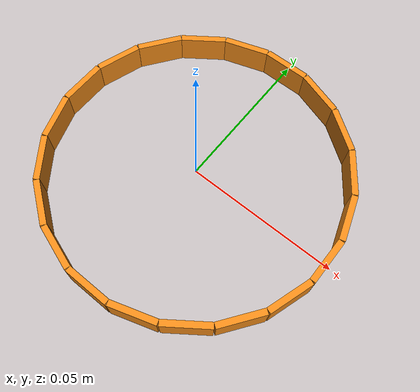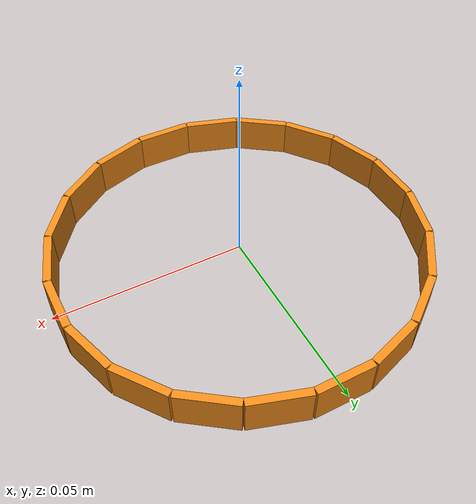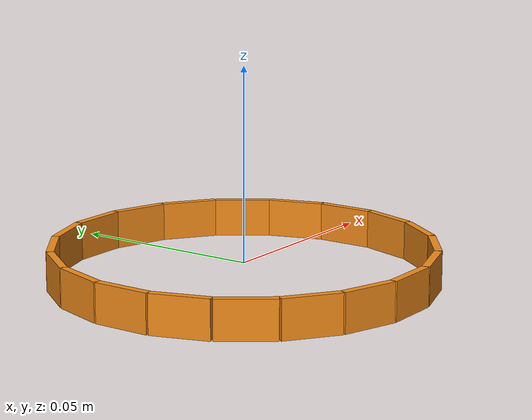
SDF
<?xml version='1.0'?>
	<sdf version='1.6'>
	  <model name='rubber_band'>
<!-- SEGMENT 0 -->
	<link name='link_hook_0'>
	  <gravity>false</gravity>
	  <pose frame=''>0.0479433991612 -0.0075 -0 0 -0 0.0</pose>
	  <inertial>
	    <mass>0.0001</mass>
	    <inertia>
	      <ixx>4e-11</ixx>
	      <ixy>0</ixy>
	      <ixz>0</ixz>
	      <iyy>4e-11</iyy>
	      <iyz>0</iyz>
	      <izz>4e-11</izz>
	    </inertia>
	    <pose frame=''>0 0 0 0 -0 0</pose>
	  </inertial>
	  <self_collide>0</self_collide>
	  <kinematic>0</kinematic>
	</link>
	<joint name='joint_pri_s0_h0' type='prismatic'>
	  <parent>link_hook_0</parent>
	  <child>link_segment_0</child>
	  <pose frame=''>0 0 0 0 -0 0</pose>
	  <axis>
	    <xyz>0 1 0</xyz>
	    <use_parent_model_frame>0</use_parent_model_frame>
	    <limit>
	      <lower>0</lower>
	      <upper>3000</upper>
	      <effort>-1</effort>
	      <velocity>-1</velocity>
	    </limit>
	    <dynamics>
	      <spring_reference>0</spring_reference>
	      <spring_stiffness>100.0</spring_stiffness>
	      <damping>30.0</damping>
	      <friction>0</friction>
	    </dynamics>
	  </axis>
	  <physics>
	    <provide_feedback>true</provide_feedback>
	    <ode>
	      <implicit_spring_damper>true</implicit_spring_damper>
	      <limit>
	        <cfm>0</cfm>
	        <erp>0.2</erp>
	      </limit>
	      <suspension>
	        <cfm>0</cfm>
	        <erp>0.2</erp>
	      </suspension>
	    </ode>
	  </physics>
	</joint>
	<link name='link_segment_0'>
	  <pose frame=''>0.0479433991612 0.0 -0 0 -0 0.0</pose>
	  <inertial>
	    <mass>0.0001</mass>
	    <inertia>
	      <ixx>2.9e-09</ixx>
	      <ixy>0</ixy>
	      <ixz>0</ixz>
	      <iyy>1.1e-09</iyy>
	      <iyz>0</iyz>
	      <izz>1.9e-09</izz>
	    </inertia>
	    <pose frame=''>0 0 0 0 -0 0</pose>
	  </inertial>
	  <self_collide>1</self_collide>
	  <kinematic>0</kinematic>
	  <visual name='visual'>
	    <pose frame=''>0 0 0 0 -0 0</pose>
	    <geometry>
	      <box>
	        <size>0.002 0.015 0.01</size>
	      </box>
	    </geometry>
	    <material>
	      <lighting>1</lighting>
	      <script>
	        <uri>file://media/materials/scripts/gazebo.material</uri>
	        <name>Gazebo/Orange</name>
	      </script>
	    </material>
	    <transparency>0</transparency>
	    <cast_shadows>1</cast_shadows>
	  </visual>
	  <collision name='collision'>
	    <laser_retro>0</laser_retro>
	    <max_contacts>10</max_contacts>
	    <pose frame=''>0 0 0 0 -0 0</pose>
	    <geometry>
	      <box>
	        <size>0.002 0.015 0.01</size>
	      </box>
	    </geometry>
	    <surface>
	      <friction>
	        <ode>
	          <mu>2</mu>
	          <mu2>2</mu2>
	          <fdir1>0 0 0</fdir1>
	          <slip1>0</slip1>
	          <slip2>0</slip2>
	        </ode>
	        <torsional>
	          <coefficient>1</coefficient>
	          <patch_radius>0</patch_radius>
	          <surface_radius>0</surface_radius>
	          <use_patch_radius>1</use_patch_radius>
	          <ode>
	            <slip>0</slip>
	          </ode>
	        </torsional>
	      </friction>
	      <bounce>
	        <restitution_coefficient>0</restitution_coefficient>
	        <threshold>1e+06</threshold>
	      </bounce>
	      <contact>
	        <collide_without_contact>0</collide_without_contact>
	        <collide_without_contact_bitmask>1</collide_without_contact_bitmask>
	        <collide_bitmask>1</collide_bitmask>
	        <ode>
	          <soft_cfm>0</soft_cfm>
	          <soft_erp>0.2</soft_erp>
	          <kp>1e+13</kp>
	          <kd>1</kd>
	          <max_vel>0.01</max_vel>
	          <min_depth>0</min_depth>
	        </ode>
	        <bullet>
	          <split_impulse>1</split_impulse>
	          <split_impulse_penetration_threshold>-0.01</split_impulse_penetration_threshold>
	          <soft_cfm>0</soft_cfm>
	          <soft_erp>0.2</soft_erp>
	          <kp>1e+13</kp>
	          <kd>1</kd>
	        </bullet>
	      </contact>
	    </surface>
	  </collision>
	</link>
<!-- SEGMENT 1 -->
	<joint name='joint_rev_s0_h1' type='revolute2'>
	  <parent>link_segment_0</parent>
	  <child>link_hook_1</child>
	  <pose frame=''>0 0 0 0 -0 0</pose>
	  <axis>
	    <xyz>1 0 0</xyz>
	    <use_parent_model_frame>0</use_parent_model_frame>
	    <limit>
	      <lower>-0.0523599</lower>
	      <upper>0.0523599</upper>
	      <effort>-1</effort>
	      <velocity>-1</velocity>
	    </limit>
	    <dynamics>
	      <spring_reference>0</spring_reference>
	      <spring_stiffness>0.1</spring_stiffness>
	      <damping>0</damping>
	      <friction>0</friction>
	    </dynamics>
	  </axis>
	  <axis2>
	    <xyz>0 0 1</xyz>
	    <use_parent_model_frame>0</use_parent_model_frame>
	    <dynamics>
	      <spring_reference>0</spring_reference>
	      <spring_stiffness>0</spring_stiffness>
	      <damping>0</damping>
	      <friction>0</friction>
	    </dynamics>
	    <limit>
	      <lower>-0.06</lower>
	      <upper>0.06</upper>
	      <effort>-1</effort>
	      <velocity>-1</velocity>
	    </limit>
	  </axis2>
	  <physics>
	    <provide_feedback>true</provide_feedback>
	    <ode>
	      <implicit_spring_damper>true</implicit_spring_damper>
	      <cfm_damping>true</cfm_damping>
	      <limit>
	        <cfm>10</cfm>
	        <erp>4</erp>
	      </limit>
	      <suspension>
	        <cfm>0.01</cfm>
	        <erp>0.2</erp>
	      </suspension>
	    </ode>
	  </physics>
	</joint>
<!-- SEGMENT 1 -->
	<link name='link_hook_1'>
	  <gravity>false</gravity>
	  <pose frame=''>0.0479145096435 0.00768240123671 -0 0 -0 0.314159265359</pose>
	  <inertial>
	    <mass>0.0001</mass>
	    <inertia>
	      <ixx>4e-11</ixx>
	      <ixy>0</ixy>
	      <ixz>0</ixz>
	      <iyy>4e-11</iyy>
	      <iyz>0</iyz>
	      <izz>4e-11</izz>
	    </inertia>
	    <pose frame=''>0 0 0 0 -0 0</pose>
	  </inertial>
	  <self_collide>0</self_collide>
	  <kinematic>0</kinematic>
	</link>
	<joint name='joint_pri_s1_h1' type='prismatic'>
	  <parent>link_hook_1</parent>
	  <child>link_segment_1</child>
	  <pose frame=''>0 0 0 0 -0 0</pose>
	  <axis>
	    <xyz>0 1 0</xyz>
	    <use_parent_model_frame>0</use_parent_model_frame>
	    <limit>
	      <lower>0</lower>
	      <upper>3000</upper>
	      <effort>-1</effort>
	      <velocity>-1</velocity>
	    </limit>
	    <dynamics>
	      <spring_reference>0</spring_reference>
	      <spring_stiffness>100.0</spring_stiffness>
	      <damping>30.0</damping>
	      <friction>0</friction>
	    </dynamics>
	  </axis>
	  <physics>
	    <provide_feedback>true</provide_feedback>
	    <ode>
	      <implicit_spring_damper>true</implicit_spring_damper>
	      <limit>
	        <cfm>0</cfm>
	        <erp>0.2</erp>
	      </limit>
	      <suspension>
	        <cfm>0</cfm>
	        <erp>0.2</erp>
	      </suspension>
	    </ode>
	  </physics>
	</joint>
	<link name='link_segment_1'>
	  <pose frame=''>0.0455968821856 0.0148153251089 -0 0 -0 0.314159265359</pose>
	  <inertial>
	    <mass>0.0001</mass>
	    <inertia>
	      <ixx>2.9e-09</ixx>
	      <ixy>0</ixy>
	      <ixz>0</ixz>
	      <iyy>1.1e-09</iyy>
	      <iyz>0</iyz>
	      <izz>1.9e-09</izz>
	    </inertia>
	    <pose frame=''>0 0 0 0 -0 0</pose>
	  </inertial>
	  <self_collide>1</self_collide>
	  <kinematic>0</kinematic>
	  <visual name='visual'>
	    <pose frame=''>0 0 0 0 -0 0</pose>
	    <geometry>
	      <box>
	        <size>0.002 0.015 0.01</size>
	      </box>
	    </geometry>
	    <material>
	      <lighting>1</lighting>
	      <script>
	        <uri>file://media/materials/scripts/gazebo.material</uri>
	        <name>Gazebo/Orange</name>
	      </script>
	    </material>
	    <transparency>0</transparency>
	    <cast_shadows>1</cast_shadows>
	  </visual>
	  <collision name='collision'>
	    <laser_retro>0</laser_retro>
	    <max_contacts>10</max_contacts>
	    <pose frame=''>0 0 0 0 -0 0</pose>
	    <geometry>
	      <box>
	        <size>0.002 0.015 0.01</size>
	      </box>
	    </geometry>
	    <surface>
	      <friction>
	        <ode>
	          <mu>2</mu>
	          <mu2>2</mu2>
	          <fdir1>0 0 0</fdir1>
	          <slip1>0</slip1>
	          <slip2>0</slip2>
	        </ode>
	        <torsional>
	          <coefficient>1</coefficient>
	          <patch_radius>0</patch_radius>
	          <surface_radius>0</surface_radius>
	          <use_patch_radius>1</use_patch_radius>
	          <ode>
	            <slip>0</slip>
	          </ode>
	        </torsional>
	      </friction>
	      <bounce>
	        <restitution_coefficient>0</restitution_coefficient>
	        <threshold>1e+06</threshold>
	      </bounce>
	      <contact>
	        <collide_without_contact>0</collide_without_contact>
	        <collide_without_contact_bitmask>1</collide_without_contact_bitmask>
	        <collide_bitmask>1</collide_bitmask>
	        <ode>
	          <soft_cfm>0</soft_cfm>
	          <soft_erp>0.2</soft_erp>
	          <kp>1e+13</kp>
	          <kd>1</kd>
	          <max_vel>0.01</max_vel>
	          <min_depth>0</min_depth>
	        </ode>
	        <bullet>
	          <split_impulse>1</split_impulse>
	          <split_impulse_penetration_threshold>-0.01</split_impulse_penetration_threshold>
	          <soft_cfm>0</soft_cfm>
	          <soft_erp>0.2</soft_erp>
	          <kp>1e+13</kp>
	          <kd>1</kd>
	        </bullet>
	      </contact>
	    </surface>
	  </collision>
	</link>
<!-- SEGMENT 2 -->
	<joint name='joint_rev_s1_h2' type='revolute2'>
	  <parent>link_segment_1</parent>
	  <child>link_hook_2</child>
	  <pose frame=''>0 0 0 0 -0 0</pose>
	  <axis>
	    <xyz>1 0 0</xyz>
	    <use_parent_model_frame>0</use_parent_model_frame>
	    <limit>
	      <lower>-0.0523599</lower>
	      <upper>0.0523599</upper>
	      <effort>-1</effort>
	      <velocity>-1</velocity>
	    </limit>
	    <dynamics>
	      <spring_reference>0</spring_reference>
	      <spring_stiffness>0.1</spring_stiffness>
	      <damping>0</damping>
	      <friction>0</friction>
	    </dynamics>
	  </axis>
	  <axis2>
	    <xyz>0 0 1</xyz>
	    <use_parent_model_frame>0</use_parent_model_frame>
	    <dynamics>
	      <spring_reference>0</spring_reference>
	      <spring_stiffness>0</spring_stiffness>
	      <damping>0</damping>
	      <friction>0</friction>
	    </dynamics>
	    <limit>
	      <lower>-0.06</lower>
	      <upper>0.06</upper>
	      <effort>-1</effort>
	      <velocity>-1</velocity>
	    </limit>
	  </axis2>
	  <physics>
	    <provide_feedback>true</provide_feedback>
	    <ode>
	      <implicit_spring_damper>true</implicit_spring_damper>
	      <cfm_damping>true</cfm_damping>
	      <limit>
	        <cfm>10</cfm>
	        <erp>4</erp>
	      </limit>
	      <suspension>
	        <cfm>0.01</cfm>
	        <erp>0.2</erp>
	      </suspension>
	    </ode>
	  </physics>
	</joint>
<!-- SEGMENT 2 -->
	<link name='link_hook_2'>
	  <gravity>false</gravity>
	  <pose frame=''>0.0431954140817 0.0221127955139 -0 0 -0 0.628318530718</pose>
	  <inertial>
	    <mass>0.0001</mass>
	    <inertia>
	      <ixx>4e-11</ixx>
	      <ixy>0</ixy>
	      <ixz>0</ixz>
	      <iyy>4e-11</iyy>
	      <iyz>0</iyz>
	      <izz>4e-11</izz>
	    </inertia>
	    <pose frame=''>0 0 0 0 -0 0</pose>
	  </inertial>
	  <self_collide>0</self_collide>
	  <kinematic>0</kinematic>
	</link>
	<joint name='joint_pri_s2_h2' type='prismatic'>
	  <parent>link_hook_2</parent>
	  <child>link_segment_2</child>
	  <pose frame=''>0 0 0 0 -0 0</pose>
	  <axis>
	    <xyz>0 1 0</xyz>
	    <use_parent_model_frame>0</use_parent_model_frame>
	    <limit>
	      <lower>0</lower>
	      <upper>3000</upper>
	      <effort>-1</effort>
	      <velocity>-1</velocity>
	    </limit>
	    <dynamics>
	      <spring_reference>0</spring_reference>
	      <spring_stiffness>100.0</spring_stiffness>
	      <damping>30.0</damping>
	      <friction>0</friction>
	    </dynamics>
	  </axis>
	  <physics>
	    <provide_feedback>true</provide_feedback>
	    <ode>
	      <implicit_spring_damper>true</implicit_spring_damper>
	      <limit>
	        <cfm>0</cfm>
	        <erp>0.2</erp>
	      </limit>
	      <suspension>
	        <cfm>0</cfm>
	        <erp>0.2</erp>
	      </suspension>
	    </ode>
	  </physics>
	</joint>
	<link name='link_segment_2'>
	  <pose frame=''>0.0387870246896 0.0281804229718 -0 0 -0 0.628318530718</pose>
	  <inertial>
	    <mass>0.0001</mass>
	    <inertia>
	      <ixx>2.9e-09</ixx>
	      <ixy>0</ixy>
	      <ixz>0</ixz>
	      <iyy>1.1e-09</iyy>
	      <iyz>0</iyz>
	      <izz>1.9e-09</izz>
	    </inertia>
	    <pose frame=''>0 0 0 0 -0 0</pose>
	  </inertial>
	  <self_collide>1</self_collide>
	  <kinematic>0</kinematic>
	  <visual name='visual'>
	    <pose frame=''>0 0 0 0 -0 0</pose>
	    <geometry>
	      <box>
	        <size>0.002 0.015 0.01</size>
	      </box>
	    </geometry>
	    <material>
	      <lighting>1</lighting>
	      <script>
	        <uri>file://media/materials/scripts/gazebo.material</uri>
	        <name>Gazebo/Orange</name>
	      </script>
	    </material>
	    <transparency>0</transparency>
	    <cast_shadows>1</cast_shadows>
	  </visual>
	  <collision name='collision'>
	    <laser_retro>0</laser_retro>
	    <max_contacts>10</max_contacts>
	    <pose frame=''>0 0 0 0 -0 0</pose>
	    <geometry>
	      <box>
	        <size>0.002 0.015 0.01</size>
	      </box>
	    </geometry>
	    <surface>
	      <friction>
	        <ode>
	          <mu>2</mu>
	          <mu2>2</mu2>
	          <fdir1>0 0 0</fdir1>
	          <slip1>0</slip1>
	          <slip2>0</slip2>
	        </ode>
	        <torsional>
	          <coefficient>1</coefficient>
	          <patch_radius>0</patch_radius>
	          <surface_radius>0</surface_radius>
	          <use_patch_radius>1</use_patch_radius>
	          <ode>
	            <slip>0</slip>
	          </ode>
	        </torsional>
	      </friction>
	      <bounce>
	        <restitution_coefficient>0</restitution_coefficient>
	        <threshold>1e+06</threshold>
	      </bounce>
	      <contact>
	        <collide_without_contact>0</collide_without_contact>
	        <collide_without_contact_bitmask>1</collide_without_contact_bitmask>
	        <collide_bitmask>1</collide_bitmask>
	        <ode>
	          <soft_cfm>0</soft_cfm>
	          <soft_erp>0.2</soft_erp>
	          <kp>1e+13</kp>
	          <kd>1</kd>
	          <max_vel>0.01</max_vel>
	          <min_depth>0</min_depth>
	        </ode>
	        <bullet>
	          <split_impulse>1</split_impulse>
	          <split_impulse_penetration_threshold>-0.01</split_impulse_penetration_threshold>
	          <soft_cfm>0</soft_cfm>
	          <soft_erp>0.2</soft_erp>
	          <kp>1e+13</kp>
	          <kd>1</kd>
	        </bullet>
	      </contact>
	    </surface>
	  </collision>
	</link>
<!-- SEGMENT 3 -->
	<joint name='joint_rev_s2_h3' type='revolute2'>
	  <parent>link_segment_2</parent>
	  <child>link_hook_3</child>
	  <pose frame=''>0 0 0 0 -0 0</pose>
	  <axis>
	    <xyz>1 0 0</xyz>
	    <use_parent_model_frame>0</use_parent_model_frame>
	    <limit>
	      <lower>-0.0523599</lower>
	      <upper>0.0523599</upper>
	      <effort>-1</effort>
	      <velocity>-1</velocity>
	    </limit>
	    <dynamics>
	      <spring_reference>0</spring_reference>
	      <spring_stiffness>0.1</spring_stiffness>
	      <damping>0</damping>
	      <friction>0</friction>
	    </dynamics>
	  </axis>
	  <axis2>
	    <xyz>0 0 1</xyz>
	    <use_parent_model_frame>0</use_parent_model_frame>
	    <dynamics>
	      <spring_reference>0</spring_reference>
	      <spring_stiffness>0</spring_stiffness>
	      <damping>0</damping>
	      <friction>0</friction>
	    </dynamics>
	    <limit>
	      <lower>-0.06</lower>
	      <upper>0.06</upper>
	      <effort>-1</effort>
	      <velocity>-1</velocity>
	    </limit>
	  </axis2>
	  <physics>
	    <provide_feedback>true</provide_feedback>
	    <ode>
	      <implicit_spring_damper>true</implicit_spring_damper>
	      <cfm_damping>true</cfm_damping>
	      <limit>
	        <cfm>10</cfm>
	        <erp>4</erp>
	      </limit>
	      <suspension>
	        <cfm>0.01</cfm>
	        <erp>0.2</erp>
	      </suspension>
	    </ode>
	  </physics>
	</joint>
<!-- SEGMENT 3 -->
	<link name='link_hook_3'>
	  <gravity>false</gravity>
	  <pose frame=''>0.0342480504296 0.0343786352974 -0 0 -0 0.942477796077</pose>
	  <inertial>
	    <mass>0.0001</mass>
	    <inertia>
	      <ixx>4e-11</ixx>
	      <ixy>0</ixy>
	      <ixz>0</ixz>
	      <iyy>4e-11</iyy>
	      <iyz>0</iyz>
	      <izz>4e-11</izz>
	    </inertia>
	    <pose frame=''>0 0 0 0 -0 0</pose>
	  </inertial>
	  <self_collide>0</self_collide>
	  <kinematic>0</kinematic>
	</link>
	<joint name='joint_pri_s3_h3' type='prismatic'>
	  <parent>link_hook_3</parent>
	  <child>link_segment_3</child>
	  <pose frame=''>0 0 0 0 -0 0</pose>
	  <axis>
	    <xyz>0 1 0</xyz>
	    <use_parent_model_frame>0</use_parent_model_frame>
	    <limit>
	      <lower>0</lower>
	      <upper>3000</upper>
	      <effort>-1</effort>
	      <velocity>-1</velocity>
	    </limit>
	    <dynamics>
	      <spring_reference>0</spring_reference>
	      <spring_stiffness>100.0</spring_stiffness>
	      <damping>30.0</damping>
	      <friction>0</friction>
	    </dynamics>
	  </axis>
	  <physics>
	    <provide_feedback>true</provide_feedback>
	    <ode>
	      <implicit_spring_damper>true</implicit_spring_damper>
	      <limit>
	        <cfm>0</cfm>
	        <erp>0.2</erp>
	      </limit>
	      <suspension>
	        <cfm>0</cfm>
	        <erp>0.2</erp>
	      </suspension>
	    </ode>
	  </physics>
	</joint>
	<link name='link_segment_3'>
	  <pose frame=''>0.0281804229718 0.0387870246896 -0 0 -0 0.942477796077</pose>
	  <inertial>
	    <mass>0.0001</mass>
	    <inertia>
	      <ixx>2.9e-09</ixx>
	      <ixy>0</ixy>
	      <ixz>0</ixz>
	      <iyy>1.1e-09</iyy>
	      <iyz>0</iyz>
	      <izz>1.9e-09</izz>
	    </inertia>
	    <pose frame=''>0 0 0 0 -0 0</pose>
	  </inertial>
	  <self_collide>1</self_collide>
	  <kinematic>0</kinematic>
	  <visual name='visual'>
	    <pose frame=''>0 0 0 0 -0 0</pose>
	    <geometry>
	      <box>
	        <size>0.002 0.015 0.01</size>
	      </box>
	    </geometry>
	    <material>
	      <lighting>1</lighting>
	      <script>
	        <uri>file://media/materials/scripts/gazebo.material</uri>
	        <name>Gazebo/Orange</name>
	      </script>
	    </material>
	    <transparency>0</transparency>
	    <cast_shadows>1</cast_shadows>
	  </visual>
	  <collision name='collision'>
	    <laser_retro>0</laser_retro>
	    <max_contacts>10</max_contacts>
	    <pose frame=''>0 0 0 0 -0 0</pose>
	    <geometry>
	      <box>
	        <size>0.002 0.015 0.01</size>
	      </box>
	    </geometry>
	    <surface>
	      <friction>
	        <ode>
	          <mu>2</mu>
	          <mu2>2</mu2>
	          <fdir1>0 0 0</fdir1>
	          <slip1>0</slip1>
	          <slip2>0</slip2>
	        </ode>
	        <torsional>
	          <coefficient>1</coefficient>
	          <patch_radius>0</patch_radius>
	          <surface_radius>0</surface_radius>
	          <use_patch_radius>1</use_patch_radius>
	          <ode>
	            <slip>0</slip>
	          </ode>
	        </torsional>
	      </friction>
	      <bounce>
	        <restitution_coefficient>0</restitution_coefficient>
	        <threshold>1e+06</threshold>
	      </bounce>
	      <contact>
	        <collide_without_contact>0</collide_without_contact>
	        <collide_without_contact_bitmask>1</collide_without_contact_bitmask>
	        <collide_bitmask>1</collide_bitmask>
	        <ode>
	          <soft_cfm>0</soft_cfm>
	          <soft_erp>0.2</soft_erp>
	          <kp>1e+13</kp>
	          <kd>1</kd>
	          <max_vel>0.01</max_vel>
	          <min_depth>0</min_depth>
	        </ode>
	        <bullet>
	          <split_impulse>1</split_impulse>
	          <split_impulse_penetration_threshold>-0.01</split_impulse_penetration_threshold>
	          <soft_cfm>0</soft_cfm>
	          <soft_erp>0.2</soft_erp>
	          <kp>1e+13</kp>
	          <kd>1</kd>
	        </bullet>
	      </contact>
	    </surface>
	  </collision>
	</link>
<!-- SEGMENT 4 -->
	<joint name='joint_rev_s3_h4' type='revolute2'>
	  <parent>link_segment_3</parent>
	  <child>link_hook_4</child>
	  <pose frame=''>0 0 0 0 -0 0</pose>
	  <axis>
	    <xyz>1 0 0</xyz>
	    <use_parent_model_frame>0</use_parent_model_frame>
	    <limit>
	      <lower>-0.0523599</lower>
	      <upper>0.0523599</upper>
	      <effort>-1</effort>
	      <velocity>-1</velocity>
	    </limit>
	    <dynamics>
	      <spring_reference>0</spring_reference>
	      <spring_stiffness>0.1</spring_stiffness>
	      <damping>0</damping>
	      <friction>0</friction>
	    </dynamics>
	  </axis>
	  <axis2>
	    <xyz>0 0 1</xyz>
	    <use_parent_model_frame>0</use_parent_model_frame>
	    <dynamics>
	      <spring_reference>0</spring_reference>
	      <spring_stiffness>0</spring_stiffness>
	      <damping>0</damping>
	      <friction>0</friction>
	    </dynamics>
	    <limit>
	      <lower>-0.06</lower>
	      <upper>0.06</upper>
	      <effort>-1</effort>
	      <velocity>-1</velocity>
	    </limit>
	  </axis2>
	  <physics>
	    <provide_feedback>true</provide_feedback>
	    <ode>
	      <implicit_spring_damper>true</implicit_spring_damper>
	      <cfm_damping>true</cfm_damping>
	      <limit>
	        <cfm>10</cfm>
	        <erp>4</erp>
	      </limit>
	      <suspension>
	        <cfm>0.01</cfm>
	        <erp>0.2</erp>
	      </suspension>
	    </ode>
	  </physics>
	</joint>
<!-- SEGMENT 4 -->
	<link name='link_hook_4'>
	  <gravity>false</gravity>
	  <pose frame=''>0.0219482489811 0.0432792547278 -0 0 -0 1.25663706144</pose>
	  <inertial>
	    <mass>0.0001</mass>
	    <inertia>
	      <ixx>4e-11</ixx>
	      <ixy>0</ixy>
	      <ixz>0</ixz>
	      <iyy>4e-11</iyy>
	      <iyz>0</iyz>
	      <izz>4e-11</izz>
	    </inertia>
	    <pose frame=''>0 0 0 0 -0 0</pose>
	  </inertial>
	  <self_collide>0</self_collide>
	  <kinematic>0</kinematic>
	</link>
	<joint name='joint_pri_s4_h4' type='prismatic'>
	  <parent>link_hook_4</parent>
	  <child>link_segment_4</child>
	  <pose frame=''>0 0 0 0 -0 0</pose>
	  <axis>
	    <xyz>0 1 0</xyz>
	    <use_parent_model_frame>0</use_parent_model_frame>
	    <limit>
	      <lower>0</lower>
	      <upper>3000</upper>
	      <effort>-1</effort>
	      <velocity>-1</velocity>
	    </limit>
	    <dynamics>
	      <spring_reference>0</spring_reference>
	      <spring_stiffness>100.0</spring_stiffness>
	      <damping>30.0</damping>
	      <friction>0</friction>
	    </dynamics>
	  </axis>
	  <physics>
	    <provide_feedback>true</provide_feedback>
	    <ode>
	      <implicit_spring_damper>true</implicit_spring_damper>
	      <limit>
	        <cfm>0</cfm>
	        <erp>0.2</erp>
	      </limit>
	      <suspension>
	        <cfm>0</cfm>
	        <erp>0.2</erp>
	      </suspension>
	    </ode>
	  </physics>
	</joint>
	<link name='link_segment_4'>
	  <pose frame=''>0.0148153251089 0.0455968821856 -0 0 -0 1.25663706144</pose>
	  <inertial>
	    <mass>0.0001</mass>
	    <inertia>
	      <ixx>2.9e-09</ixx>
	      <ixy>0</ixy>
	      <ixz>0</ixz>
	      <iyy>1.1e-09</iyy>
	      <iyz>0</iyz>
	      <izz>1.9e-09</izz>
	    </inertia>
	    <pose frame=''>0 0 0 0 -0 0</pose>
	  </inertial>
	  <self_collide>1</self_collide>
	  <kinematic>0</kinematic>
	  <visual name='visual'>
	    <pose frame=''>0 0 0 0 -0 0</pose>
	    <geometry>
	      <box>
	        <size>0.002 0.015 0.01</size>
	      </box>
	    </geometry>
	    <material>
	      <lighting>1</lighting>
	      <script>
	        <uri>file://media/materials/scripts/gazebo.material</uri>
	        <name>Gazebo/Orange</name>
	      </script>
	    </material>
	    <transparency>0</transparency>
	    <cast_shadows>1</cast_shadows>
	  </visual>
	  <collision name='collision'>
	    <laser_retro>0</laser_retro>
	    <max_contacts>10</max_contacts>
	    <pose frame=''>0 0 0 0 -0 0</pose>
	    <geometry>
	      <box>
	        <size>0.002 0.015 0.01</size>
	      </box>
	    </geometry>
	    <surface>
	      <friction>
	        <ode>
	          <mu>2</mu>
	          <mu2>2</mu2>
	          <fdir1>0 0 0</fdir1>
	          <slip1>0</slip1>
	          <slip2>0</slip2>
	        </ode>
	        <torsional>
	          <coefficient>1</coefficient>
	          <patch_radius>0</patch_radius>
	          <surface_radius>0</surface_radius>
	          <use_patch_radius>1</use_patch_radius>
	          <ode>
	            <slip>0</slip>
	          </ode>
	        </torsional>
	      </friction>
	      <bounce>
	        <restitution_coefficient>0</restitution_coefficient>
	        <threshold>1e+06</threshold>
	      </bounce>
	      <contact>
	        <collide_without_contact>0</collide_without_contact>
	        <collide_without_contact_bitmask>1</collide_without_contact_bitmask>
	        <collide_bitmask>1</collide_bitmask>
	        <ode>
	          <soft_cfm>0</soft_cfm>
	          <soft_erp>0.2</soft_erp>
	          <kp>1e+13</kp>
	          <kd>1</kd>
	          <max_vel>0.01</max_vel>
	          <min_depth>0</min_depth>
	        </ode>
	        <bullet>
	          <split_impulse>1</split_impulse>
	          <split_impulse_penetration_threshold>-0.01</split_impulse_penetration_threshold>
	          <soft_cfm>0</soft_cfm>
	          <soft_erp>0.2</soft_erp>
	          <kp>1e+13</kp>
	          <kd>1</kd>
	        </bullet>
	      </contact>
	    </surface>
	  </collision>
	</link>
<!-- SEGMENT 5 -->
	<joint name='joint_rev_s4_h5' type='revolute2'>
	  <parent>link_segment_4</parent>
	  <child>link_hook_5</child>
	  <pose frame=''>0 0 0 0 -0 0</pose>
	  <axis>
	    <xyz>1 0 0</xyz>
	    <use_parent_model_frame>0</use_parent_model_frame>
	    <limit>
	      <lower>-0.0523599</lower>
	      <upper>0.0523599</upper>
	      <effort>-1</effort>
	      <velocity>-1</velocity>
	    </limit>
	    <dynamics>
	      <spring_reference>0</spring_reference>
	      <spring_stiffness>0.1</spring_stiffness>
	      <damping>0</damping>
	      <friction>0</friction>
	    </dynamics>
	  </axis>
	  <axis2>
	    <xyz>0 0 1</xyz>
	    <use_parent_model_frame>0</use_parent_model_frame>
	    <dynamics>
	      <spring_reference>0</spring_reference>
	      <spring_stiffness>0</spring_stiffness>
	      <damping>0</damping>
	      <friction>0</friction>
	    </dynamics>
	    <limit>
	      <lower>-0.06</lower>
	      <upper>0.06</upper>
	      <effort>-1</effort>
	      <velocity>-1</velocity>
	    </limit>
	  </axis2>
	  <physics>
	    <provide_feedback>true</provide_feedback>
	    <ode>
	      <implicit_spring_damper>true</implicit_spring_damper>
	      <cfm_damping>true</cfm_damping>
	      <limit>
	        <cfm>10</cfm>
	        <erp>4</erp>
	      </limit>
	      <suspension>
	        <cfm>0.01</cfm>
	        <erp>0.2</erp>
	      </suspension>
	    </ode>
	  </physics>
	</joint>
<!-- SEGMENT 5 -->
	<link name='link_hook_5'>
	  <gravity>false</gravity>
	  <pose frame=''>0.0075 0.0479433991612 -0 0 -0 1.57079632679</pose>
	  <inertial>
	    <mass>0.0001</mass>
	    <inertia>
	      <ixx>4e-11</ixx>
	      <ixy>0</ixy>
	      <ixz>0</ixz>
	      <iyy>4e-11</iyy>
	      <iyz>0</iyz>
	      <izz>4e-11</izz>
	    </inertia>
	    <pose frame=''>0 0 0 0 -0 0</pose>
	  </inertial>
	  <self_collide>0</self_collide>
	  <kinematic>0</kinematic>
	</link>
	<joint name='joint_pri_s5_h5' type='prismatic'>
	  <parent>link_hook_5</parent>
	  <child>link_segment_5</child>
	  <pose frame=''>0 0 0 0 -0 0</pose>
	  <axis>
	    <xyz>0 1 0</xyz>
	    <use_parent_model_frame>0</use_parent_model_frame>
	    <limit>
	      <lower>0</lower>
	      <upper>3000</upper>
	      <effort>-1</effort>
	      <velocity>-1</velocity>
	    </limit>
	    <dynamics>
	      <spring_reference>0</spring_reference>
	      <spring_stiffness>100.0</spring_stiffness>
	      <damping>30.0</damping>
	      <friction>0</friction>
	    </dynamics>
	  </axis>
	  <physics>
	    <provide_feedback>true</provide_feedback>
	    <ode>
	      <implicit_spring_damper>true</implicit_spring_damper>
	      <limit>
	        <cfm>0</cfm>
	        <erp>0.2</erp>
	      </limit>
	      <suspension>
	        <cfm>0</cfm>
	        <erp>0.2</erp>
	      </suspension>
	    </ode>
	  </physics>
	</joint>
	<link name='link_segment_5'>
	  <pose frame=''>2.93568651615e-18 0.0479433991612 -0 0 -0 1.57079632679</pose>
	  <inertial>
	    <mass>0.0001</mass>
	    <inertia>
	      <ixx>2.9e-09</ixx>
	      <ixy>0</ixy>
	      <ixz>0</ixz>
	      <iyy>1.1e-09</iyy>
	      <iyz>0</iyz>
	      <izz>1.9e-09</izz>
	    </inertia>
	    <pose frame=''>0 0 0 0 -0 0</pose>
	  </inertial>
	  <self_collide>1</self_collide>
	  <kinematic>0</kinematic>
	  <visual name='visual'>
	    <pose frame=''>0 0 0 0 -0 0</pose>
	    <geometry>
	      <box>
	        <size>0.002 0.015 0.01</size>
	      </box>
	    </geometry>
	    <material>
	      <lighting>1</lighting>
	      <script>
	        <uri>file://media/materials/scripts/gazebo.material</uri>
	        <name>Gazebo/Orange</name>
	      </script>
	    </material>
	    <transparency>0</transparency>
	    <cast_shadows>1</cast_shadows>
	  </visual>
	  <collision name='collision'>
	    <laser_retro>0</laser_retro>
	    <max_contacts>10</max_contacts>
	    <pose frame=''>0 0 0 0 -0 0</pose>
	    <geometry>
	      <box>
	        <size>0.002 0.015 0.01</size>
	      </box>
	    </geometry>
	    <surface>
	      <friction>
	        <ode>
	          <mu>2</mu>
	          <mu2>2</mu2>
	          <fdir1>0 0 0</fdir1>
	          <slip1>0</slip1>
	          <slip2>0</slip2>
	        </ode>
	        <torsional>
	          <coefficient>1</coefficient>
	          <patch_radius>0</patch_radius>
	          <surface_radius>0</surface_radius>
	          <use_patch_radius>1</use_patch_radius>
	          <ode>
	            <slip>0</slip>
	          </ode>
	        </torsional>
	      </friction>
	      <bounce>
	        <restitution_coefficient>0</restitution_coefficient>
	        <threshold>1e+06</threshold>
	      </bounce>
	      <contact>
	        <collide_without_contact>0</collide_without_contact>
	        <collide_without_contact_bitmask>1</collide_without_contact_bitmask>
	        <collide_bitmask>1</collide_bitmask>
	        <ode>
	          <soft_cfm>0</soft_cfm>
	          <soft_erp>0.2</soft_erp>
	          <kp>1e+13</kp>
	          <kd>1</kd>
	          <max_vel>0.01</max_vel>
	          <min_depth>0</min_depth>
	        </ode>
	        <bullet>
	          <split_impulse>1</split_impulse>
	          <split_impulse_penetration_threshold>-0.01</split_impulse_penetration_threshold>
	          <soft_cfm>0</soft_cfm>
	          <soft_erp>0.2</soft_erp>
	          <kp>1e+13</kp>
	          <kd>1</kd>
	        </bullet>
	      </contact>
	    </surface>
	  </collision>
	</link>
<!-- SEGMENT 6 -->
	<joint name='joint_rev_s5_h6' type='revolute2'>
	  <parent>link_segment_5</parent>
	  <child>link_hook_6</child>
	  <pose frame=''>0 0 0 0 -0 0</pose>
	  <axis>
	    <xyz>1 0 0</xyz>
	    <use_parent_model_frame>0</use_parent_model_frame>
	    <limit>
	      <lower>-0.0523599</lower>
	      <upper>0.0523599</upper>
	      <effort>-1</effort>
	      <velocity>-1</velocity>
	    </limit>
	    <dynamics>
	      <spring_reference>0</spring_reference>
	      <spring_stiffness>0.1</spring_stiffness>
	      <damping>0</damping>
	      <friction>0</friction>
	    </dynamics>
	  </axis>
	  <axis2>
	    <xyz>0 0 1</xyz>
	    <use_parent_model_frame>0</use_parent_model_frame>
	    <dynamics>
	      <spring_reference>0</spring_reference>
	      <spring_stiffness>0</spring_stiffness>
	      <damping>0</damping>
	      <friction>0</friction>
	    </dynamics>
	    <limit>
	      <lower>-0.06</lower>
	      <upper>0.06</upper>
	      <effort>-1</effort>
	      <velocity>-1</velocity>
	    </limit>
	  </axis2>
	  <physics>
	    <provide_feedback>true</provide_feedback>
	    <ode>
	      <implicit_spring_damper>true</implicit_spring_damper>
	      <cfm_damping>true</cfm_damping>
	      <limit>
	        <cfm>10</cfm>
	        <erp>4</erp>
	      </limit>
	      <suspension>
	        <cfm>0.01</cfm>
	        <erp>0.2</erp>
	      </suspension>
	    </ode>
	  </physics>
	</joint>
<!-- SEGMENT 6 -->
	<link name='link_hook_6'>
	  <gravity>false</gravity>
	  <pose frame=''>-0.00768240123671 0.0479145096435 -0 0 -0 1.88495559215</pose>
	  <inertial>
	    <mass>0.0001</mass>
	    <inertia>
	      <ixx>4e-11</ixx>
	      <ixy>0</ixy>
	      <ixz>0</ixz>
	      <iyy>4e-11</iyy>
	      <iyz>0</iyz>
	      <izz>4e-11</izz>
	    </inertia>
	    <pose frame=''>0 0 0 0 -0 0</pose>
	  </inertial>
	  <self_collide>0</self_collide>
	  <kinematic>0</kinematic>
	</link>
	<joint name='joint_pri_s6_h6' type='prismatic'>
	  <parent>link_hook_6</parent>
	  <child>link_segment_6</child>
	  <pose frame=''>0 0 0 0 -0 0</pose>
	  <axis>
	    <xyz>0 1 0</xyz>
	    <use_parent_model_frame>0</use_parent_model_frame>
	    <limit>
	      <lower>0</lower>
	      <upper>3000</upper>
	      <effort>-1</effort>
	      <velocity>-1</velocity>
	    </limit>
	    <dynamics>
	      <spring_reference>0</spring_reference>
	      <spring_stiffness>100.0</spring_stiffness>
	      <damping>30.0</damping>
	      <friction>0</friction>
	    </dynamics>
	  </axis>
	  <physics>
	    <provide_feedback>true</provide_feedback>
	    <ode>
	      <implicit_spring_damper>true</implicit_spring_damper>
	      <limit>
	        <cfm>0</cfm>
	        <erp>0.2</erp>
	      </limit>
	      <suspension>
	        <cfm>0</cfm>
	        <erp>0.2</erp>
	      </suspension>
	    </ode>
	  </physics>
	</joint>
	<link name='link_segment_6'>
	  <pose frame=''>-0.0148153251089 0.0455968821856 -0 0 -0 1.88495559215</pose>
	  <inertial>
	    <mass>0.0001</mass>
	    <inertia>
	      <ixx>2.9e-09</ixx>
	      <ixy>0</ixy>
	      <ixz>0</ixz>
	      <iyy>1.1e-09</iyy>
	      <iyz>0</iyz>
	      <izz>1.9e-09</izz>
	    </inertia>
	    <pose frame=''>0 0 0 0 -0 0</pose>
	  </inertial>
	  <self_collide>1</self_collide>
	  <kinematic>0</kinematic>
	  <visual name='visual'>
	    <pose frame=''>0 0 0 0 -0 0</pose>
	    <geometry>
	      <box>
	        <size>0.002 0.015 0.01</size>
	      </box>
	    </geometry>
	    <material>
	      <lighting>1</lighting>
	      <script>
	        <uri>file://media/materials/scripts/gazebo.material</uri>
	        <name>Gazebo/Orange</name>
	      </script>
	    </material>
	    <transparency>0</transparency>
	    <cast_shadows>1</cast_shadows>
	  </visual>
	  <collision name='collision'>
	    <laser_retro>0</laser_retro>
	    <max_contacts>10</max_contacts>
	    <pose frame=''>0 0 0 0 -0 0</pose>
	    <geometry>
	      <box>
	        <size>0.002 0.015 0.01</size>
	      </box>
	    </geometry>
	    <surface>
	      <friction>
	        <ode>
	          <mu>2</mu>
	          <mu2>2</mu2>
	          <fdir1>0 0 0</fdir1>
	          <slip1>0</slip1>
	          <slip2>0</slip2>
	        </ode>
	        <torsional>
	          <coefficient>1</coefficient>
	          <patch_radius>0</patch_radius>
	          <surface_radius>0</surface_radius>
	          <use_patch_radius>1</use_patch_radius>
	          <ode>
	            <slip>0</slip>
	          </ode>
	        </torsional>
	      </friction>
	      <bounce>
	        <restitution_coefficient>0</restitution_coefficient>
	        <threshold>1e+06</threshold>
	      </bounce>
	      <contact>
	        <collide_without_contact>0</collide_without_contact>
	        <collide_without_contact_bitmask>1</collide_without_contact_bitmask>
	        <collide_bitmask>1</collide_bitmask>
	        <ode>
	          <soft_cfm>0</soft_cfm>
	          <soft_erp>0.2</soft_erp>
	          <kp>1e+13</kp>
	          <kd>1</kd>
	          <max_vel>0.01</max_vel>
	          <min_depth>0</min_depth>
	        </ode>
	        <bullet>
	          <split_impulse>1</split_impulse>
	          <split_impulse_penetration_threshold>-0.01</split_impulse_penetration_threshold>
	          <soft_cfm>0</soft_cfm>
	          <soft_erp>0.2</soft_erp>
	          <kp>1e+13</kp>
	          <kd>1</kd>
	        </bullet>
	      </contact>
	    </surface>
	  </collision>
	</link>
<!-- SEGMENT 7 -->
	<joint name='joint_rev_s6_h7' type='revolute2'>
	  <parent>link_segment_6</parent>
	  <child>link_hook_7</child>
	  <pose frame=''>0 0 0 0 -0 0</pose>
	  <axis>
	    <xyz>1 0 0</xyz>
	    <use_parent_model_frame>0</use_parent_model_frame>
	    <limit>
	      <lower>-0.0523599</lower>
	      <upper>0.0523599</upper>
	      <effort>-1</effort>
	      <velocity>-1</velocity>
	    </limit>
	    <dynamics>
	      <spring_reference>0</spring_reference>
	      <spring_stiffness>0.1</spring_stiffness>
	      <damping>0</damping>
	      <friction>0</friction>
	    </dynamics>
	  </axis>
	  <axis2>
	    <xyz>0 0 1</xyz>
	    <use_parent_model_frame>0</use_parent_model_frame>
	    <dynamics>
	      <spring_reference>0</spring_reference>
	      <spring_stiffness>0</spring_stiffness>
	      <damping>0</damping>
	      <friction>0</friction>
	    </dynamics>
	    <limit>
	      <lower>-0.06</lower>
	      <upper>0.06</upper>
	      <effort>-1</effort>
	      <velocity>-1</velocity>
	    </limit>
	  </axis2>
	  <physics>
	    <provide_feedback>true</provide_feedback>
	    <ode>
	      <implicit_spring_damper>true</implicit_spring_damper>
	      <cfm_damping>true</cfm_damping>
	      <limit>
	        <cfm>10</cfm>
	        <erp>4</erp>
	      </limit>
	      <suspension>
	        <cfm>0.01</cfm>
	        <erp>0.2</erp>
	      </suspension>
	    </ode>
	  </physics>
	</joint>
<!-- SEGMENT 7 -->
	<link name='link_hook_7'>
	  <gravity>false</gravity>
	  <pose frame=''>-0.0221127955139 0.0431954140817 -0 0 -0 2.19911485751</pose>
	  <inertial>
	    <mass>0.0001</mass>
	    <inertia>
	      <ixx>4e-11</ixx>
	      <ixy>0</ixy>
	      <ixz>0</ixz>
	      <iyy>4e-11</iyy>
	      <iyz>0</iyz>
	      <izz>4e-11</izz>
	    </inertia>
	    <pose frame=''>0 0 0 0 -0 0</pose>
	  </inertial>
	  <self_collide>0</self_collide>
	  <kinematic>0</kinematic>
	</link>
	<joint name='joint_pri_s7_h7' type='prismatic'>
	  <parent>link_hook_7</parent>
	  <child>link_segment_7</child>
	  <pose frame=''>0 0 0 0 -0 0</pose>
	  <axis>
	    <xyz>0 1 0</xyz>
	    <use_parent_model_frame>0</use_parent_model_frame>
	    <limit>
	      <lower>0</lower>
	      <upper>3000</upper>
	      <effort>-1</effort>
	      <velocity>-1</velocity>
	    </limit>
	    <dynamics>
	      <spring_reference>0</spring_reference>
	      <spring_stiffness>100.0</spring_stiffness>
	      <damping>30.0</damping>
	      <friction>0</friction>
	    </dynamics>
	  </axis>
	  <physics>
	    <provide_feedback>true</provide_feedback>
	    <ode>
	      <implicit_spring_damper>true</implicit_spring_damper>
	      <limit>
	        <cfm>0</cfm>
	        <erp>0.2</erp>
	      </limit>
	      <suspension>
	        <cfm>0</cfm>
	        <erp>0.2</erp>
	      </suspension>
	    </ode>
	  </physics>
	</joint>
	<link name='link_segment_7'>
	  <pose frame=''>-0.0281804229718 0.0387870246896 -0 0 -0 2.19911485751</pose>
	  <inertial>
	    <mass>0.0001</mass>
	    <inertia>
	      <ixx>2.9e-09</ixx>
	      <ixy>0</ixy>
	      <ixz>0</ixz>
	      <iyy>1.1e-09</iyy>
	      <iyz>0</iyz>
	      <izz>1.9e-09</izz>
	    </inertia>
	    <pose frame=''>0 0 0 0 -0 0</pose>
	  </inertial>
	  <self_collide>1</self_collide>
	  <kinematic>0</kinematic>
	  <visual name='visual'>
	    <pose frame=''>0 0 0 0 -0 0</pose>
	    <geometry>
	      <box>
	        <size>0.002 0.015 0.01</size>
	      </box>
	    </geometry>
	    <material>
	      <lighting>1</lighting>
	      <script>
	        <uri>file://media/materials/scripts/gazebo.material</uri>
	        <name>Gazebo/Orange</name>
	      </script>
	    </material>
	    <transparency>0</transparency>
	    <cast_shadows>1</cast_shadows>
	  </visual>
	  <collision name='collision'>
	    <laser_retro>0</laser_retro>
	    <max_contacts>10</max_contacts>
	    <pose frame=''>0 0 0 0 -0 0</pose>
	    <geometry>
	      <box>
	        <size>0.002 0.015 0.01</size>
	      </box>
	    </geometry>
	    <surface>
	      <friction>
	        <ode>
	          <mu>2</mu>
	          <mu2>2</mu2>
	          <fdir1>0 0 0</fdir1>
	          <slip1>0</slip1>
	          <slip2>0</slip2>
	        </ode>
	        <torsional>
	          <coefficient>1</coefficient>
	          <patch_radius>0</patch_radius>
	          <surface_radius>0</surface_radius>
	          <use_patch_radius>1</use_patch_radius>
	          <ode>
	            <slip>0</slip>
	          </ode>
	        </torsional>
	      </friction>
	      <bounce>
	        <restitution_coefficient>0</restitution_coefficient>
	        <threshold>1e+06</threshold>
	      </bounce>
	      <contact>
	        <collide_without_contact>0</collide_without_contact>
	        <collide_without_contact_bitmask>1</collide_without_contact_bitmask>
	        <collide_bitmask>1</collide_bitmask>
	        <ode>
	          <soft_cfm>0</soft_cfm>
	          <soft_erp>0.2</soft_erp>
	          <kp>1e+13</kp>
	          <kd>1</kd>
	          <max_vel>0.01</max_vel>
	          <min_depth>0</min_depth>
	        </ode>
	        <bullet>
	          <split_impulse>1</split_impulse>
	          <split_impulse_penetration_threshold>-0.01</split_impulse_penetration_threshold>
	          <soft_cfm>0</soft_cfm>
	          <soft_erp>0.2</soft_erp>
	          <kp>1e+13</kp>
	          <kd>1</kd>
	        </bullet>
	      </contact>
	    </surface>
	  </collision>
	</link>
<!-- SEGMENT 8 -->
	<joint name='joint_rev_s7_h8' type='revolute2'>
	  <parent>link_segment_7</parent>
	  <child>link_hook_8</child>
	  <pose frame=''>0 0 0 0 -0 0</pose>
	  <axis>
	    <xyz>1 0 0</xyz>
	    <use_parent_model_frame>0</use_parent_model_frame>
	    <limit>
	      <lower>-0.0523599</lower>
	      <upper>0.0523599</upper>
	      <effort>-1</effort>
	      <velocity>-1</velocity>
	    </limit>
	    <dynamics>
	      <spring_reference>0</spring_reference>
	      <spring_stiffness>0.1</spring_stiffness>
	      <damping>0</damping>
	      <friction>0</friction>
	    </dynamics>
	  </axis>
	  <axis2>
	    <xyz>0 0 1</xyz>
	    <use_parent_model_frame>0</use_parent_model_frame>
	    <dynamics>
	      <spring_reference>0</spring_reference>
	      <spring_stiffness>0</spring_stiffness>
	      <damping>0</damping>
	      <friction>0</friction>
	    </dynamics>
	    <limit>
	      <lower>-0.06</lower>
	      <upper>0.06</upper>
	      <effort>-1</effort>
	      <velocity>-1</velocity>
	    </limit>
	  </axis2>
	  <physics>
	    <provide_feedback>true</provide_feedback>
	    <ode>
	      <implicit_spring_damper>true</implicit_spring_damper>
	      <cfm_damping>true</cfm_damping>
	      <limit>
	        <cfm>10</cfm>
	        <erp>4</erp>
	      </limit>
	      <suspension>
	        <cfm>0.01</cfm>
	        <erp>0.2</erp>
	      </suspension>
	    </ode>
	  </physics>
	</joint>
<!-- SEGMENT 8 -->
	<link name='link_hook_8'>
	  <gravity>false</gravity>
	  <pose frame=''>-0.0343786352974 0.0342480504296 -0 0 -0 2.51327412287</pose>
	  <inertial>
	    <mass>0.0001</mass>
	    <inertia>
	      <ixx>4e-11</ixx>
	      <ixy>0</ixy>
	      <ixz>0</ixz>
	      <iyy>4e-11</iyy>
	      <iyz>0</iyz>
	      <izz>4e-11</izz>
	    </inertia>
	    <pose frame=''>0 0 0 0 -0 0</pose>
	  </inertial>
	  <self_collide>0</self_collide>
	  <kinematic>0</kinematic>
	</link>
	<joint name='joint_pri_s8_h8' type='prismatic'>
	  <parent>link_hook_8</parent>
	  <child>link_segment_8</child>
	  <pose frame=''>0 0 0 0 -0 0</pose>
	  <axis>
	    <xyz>0 1 0</xyz>
	    <use_parent_model_frame>0</use_parent_model_frame>
	    <limit>
	      <lower>0</lower>
	      <upper>3000</upper>
	      <effort>-1</effort>
	      <velocity>-1</velocity>
	    </limit>
	    <dynamics>
	      <spring_reference>0</spring_reference>
	      <spring_stiffness>100.0</spring_stiffness>
	      <damping>30.0</damping>
	      <friction>0</friction>
	    </dynamics>
	  </axis>
	  <physics>
	    <provide_feedback>true</provide_feedback>
	    <ode>
	      <implicit_spring_damper>true</implicit_spring_damper>
	      <limit>
	        <cfm>0</cfm>
	        <erp>0.2</erp>
	      </limit>
	      <suspension>
	        <cfm>0</cfm>
	        <erp>0.2</erp>
	      </suspension>
	    </ode>
	  </physics>
	</joint>
	<link name='link_segment_8'>
	  <pose frame=''>-0.0387870246896 0.0281804229718 -0 0 -0 2.51327412287</pose>
	  <inertial>
	    <mass>0.0001</mass>
	    <inertia>
	      <ixx>2.9e-09</ixx>
	      <ixy>0</ixy>
	      <ixz>0</ixz>
	      <iyy>1.1e-09</iyy>
	      <iyz>0</iyz>
	      <izz>1.9e-09</izz>
	    </inertia>
	    <pose frame=''>0 0 0 0 -0 0</pose>
	  </inertial>
	  <self_collide>1</self_collide>
	  <kinematic>0</kinematic>
	  <visual name='visual'>
	    <pose frame=''>0 0 0 0 -0 0</pose>
	    <geometry>
	      <box>
	        <size>0.002 0.015 0.01</size>
	      </box>
	    </geometry>
	    <material>
	      <lighting>1</lighting>
	      <script>
	        <uri>file://media/materials/scripts/gazebo.material</uri>
	        <name>Gazebo/Orange</name>
	      </script>
	    </material>
	    <transparency>0</transparency>
	    <cast_shadows>1</cast_shadows>
	  </visual>
	  <collision name='collision'>
	    <laser_retro>0</laser_retro>
	    <max_contacts>10</max_contacts>
	    <pose frame=''>0 0 0 0 -0 0</pose>
	    <geometry>
	      <box>
	        <size>0.002 0.015 0.01</size>
	      </box>
	    </geometry>
	    <surface>
	      <friction>
	        <ode>
	          <mu>2</mu>
	          <mu2>2</mu2>
	          <fdir1>0 0 0</fdir1>
	          <slip1>0</slip1>
	          <slip2>0</slip2>
	        </ode>
	        <torsional>
	          <coefficient>1</coefficient>
	          <patch_radius>0</patch_radius>
	          <surface_radius>0</surface_radius>
	          <use_patch_radius>1</use_patch_radius>
	          <ode>
	            <slip>0</slip>
	          </ode>
	        </torsional>
	      </friction>
	      <bounce>
	        <restitution_coefficient>0</restitution_coefficient>
	        <threshold>1e+06</threshold>
	      </bounce>
	      <contact>
	        <collide_without_contact>0</collide_without_contact>
	        <collide_without_contact_bitmask>1</collide_without_contact_bitmask>
	        <collide_bitmask>1</collide_bitmask>
	        <ode>
	          <soft_cfm>0</soft_cfm>
	          <soft_erp>0.2</soft_erp>
	          <kp>1e+13</kp>
	          <kd>1</kd>
	          <max_vel>0.01</max_vel>
	          <min_depth>0</min_depth>
	        </ode>
	        <bullet>
	          <split_impulse>1</split_impulse>
	          <split_impulse_penetration_threshold>-0.01</split_impulse_penetration_threshold>
	          <soft_cfm>0</soft_cfm>
	          <soft_erp>0.2</soft_erp>
	          <kp>1e+13</kp>
	          <kd>1</kd>
	        </bullet>
	      </contact>
	    </surface>
	  </collision>
	</link>
<!-- SEGMENT 9 -->
	<joint name='joint_rev_s8_h9' type='revolute2'>
	  <parent>link_segment_8</parent>
	  <child>link_hook_9</child>
	  <pose frame=''>0 0 0 0 -0 0</pose>
	  <axis>
	    <xyz>1 0 0</xyz>
	    <use_parent_model_frame>0</use_parent_model_frame>
	    <limit>
	      <lower>-0.0523599</lower>
	      <upper>0.0523599</upper>
	      <effort>-1</effort>
	      <velocity>-1</velocity>
	    </limit>
	    <dynamics>
	      <spring_reference>0</spring_reference>
	      <spring_stiffness>0.1</spring_stiffness>
	      <damping>0</damping>
	      <friction>0</friction>
	    </dynamics>
	  </axis>
	  <axis2>
	    <xyz>0 0 1</xyz>
	    <use_parent_model_frame>0</use_parent_model_frame>
	    <dynamics>
	      <spring_reference>0</spring_reference>
	      <spring_stiffness>0</spring_stiffness>
	      <damping>0</damping>
	      <friction>0</friction>
	    </dynamics>
	    <limit>
	      <lower>-0.06</lower>
	      <upper>0.06</upper>
	      <effort>-1</effort>
	      <velocity>-1</velocity>
	    </limit>
	  </axis2>
	  <physics>
	    <provide_feedback>true</provide_feedback>
	    <ode>
	      <implicit_spring_damper>true</implicit_spring_damper>
	      <cfm_damping>true</cfm_damping>
	      <limit>
	        <cfm>10</cfm>
	        <erp>4</erp>
	      </limit>
	      <suspension>
	        <cfm>0.01</cfm>
	        <erp>0.2</erp>
	      </suspension>
	    </ode>
	  </physics>
	</joint>
<!-- SEGMENT 9 -->
	<link name='link_hook_9'>
	  <gravity>false</gravity>
	  <pose frame=''>-0.0432792547278 0.0219482489811 -0 0 -0 2.82743338823</pose>
	  <inertial>
	    <mass>0.0001</mass>
	    <inertia>
	      <ixx>4e-11</ixx>
	      <ixy>0</ixy>
	      <ixz>0</ixz>
	      <iyy>4e-11</iyy>
	      <iyz>0</iyz>
	      <izz>4e-11</izz>
	    </inertia>
	    <pose frame=''>0 0 0 0 -0 0</pose>
	  </inertial>
	  <self_collide>0</self_collide>
	  <kinematic>0</kinematic>
	</link>
	<joint name='joint_pri_s9_h9' type='prismatic'>
	  <parent>link_hook_9</parent>
	  <child>link_segment_9</child>
	  <pose frame=''>0 0 0 0 -0 0</pose>
	  <axis>
	    <xyz>0 1 0</xyz>
	    <use_parent_model_frame>0</use_parent_model_frame>
	    <limit>
	      <lower>0</lower>
	      <upper>3000</upper>
	      <effort>-1</effort>
	      <velocity>-1</velocity>
	    </limit>
	    <dynamics>
	      <spring_reference>0</spring_reference>
	      <spring_stiffness>100.0</spring_stiffness>
	      <damping>30.0</damping>
	      <friction>0</friction>
	    </dynamics>
	  </axis>
	  <physics>
	    <provide_feedback>true</provide_feedback>
	    <ode>
	      <implicit_spring_damper>true</implicit_spring_damper>
	      <limit>
	        <cfm>0</cfm>
	        <erp>0.2</erp>
	      </limit>
	      <suspension>
	        <cfm>0</cfm>
	        <erp>0.2</erp>
	      </suspension>
	    </ode>
	  </physics>
	</joint>
	<link name='link_segment_9'>
	  <pose frame=''>-0.0455968821856 0.0148153251089 -0 0 -0 2.82743338823</pose>
	  <inertial>
	    <mass>0.0001</mass>
	    <inertia>
	      <ixx>2.9e-09</ixx>
	      <ixy>0</ixy>
	      <ixz>0</ixz>
	      <iyy>1.1e-09</iyy>
	      <iyz>0</iyz>
	      <izz>1.9e-09</izz>
	    </inertia>
	    <pose frame=''>0 0 0 0 -0 0</pose>
	  </inertial>
	  <self_collide>1</self_collide>
	  <kinematic>0</kinematic>
	  <visual name='visual'>
	    <pose frame=''>0 0 0 0 -0 0</pose>
	    <geometry>
	      <box>
	        <size>0.002 0.015 0.01</size>
	      </box>
	    </geometry>
	    <material>
	      <lighting>1</lighting>
	      <script>
	        <uri>file://media/materials/scripts/gazebo.material</uri>
	        <name>Gazebo/Orange</name>
	      </script>
	    </material>
	    <transparency>0</transparency>
	    <cast_shadows>1</cast_shadows>
	  </visual>
	  <collision name='collision'>
	    <laser_retro>0</laser_retro>
	    <max_contacts>10</max_contacts>
	    <pose frame=''>0 0 0 0 -0 0</pose>
	    <geometry>
	      <box>
	        <size>0.002 0.015 0.01</size>
	      </box>
	    </geometry>
	    <surface>
	      <friction>
	        <ode>
	          <mu>2</mu>
	          <mu2>2</mu2>
	          <fdir1>0 0 0</fdir1>
	          <slip1>0</slip1>
	          <slip2>0</slip2>
	        </ode>
	        <torsional>
	          <coefficient>1</coefficient>
	          <patch_radius>0</patch_radius>
	          <surface_radius>0</surface_radius>
	          <use_patch_radius>1</use_patch_radius>
	          <ode>
	            <slip>0</slip>
	          </ode>
	        </torsional>
	      </friction>
	      <bounce>
	        <restitution_coefficient>0</restitution_coefficient>
	        <threshold>1e+06</threshold>
	      </bounce>
	      <contact>
	        <collide_without_contact>0</collide_without_contact>
	        <collide_without_contact_bitmask>1</collide_without_contact_bitmask>
	        <collide_bitmask>1</collide_bitmask>
	        <ode>
	          <soft_cfm>0</soft_cfm>
	          <soft_erp>0.2</soft_erp>
	          <kp>1e+13</kp>
	          <kd>1</kd>
	          <max_vel>0.01</max_vel>
	          <min_depth>0</min_depth>
	        </ode>
	        <bullet>
	          <split_impulse>1</split_impulse>
	          <split_impulse_penetration_threshold>-0.01</split_impulse_penetration_threshold>
	          <soft_cfm>0</soft_cfm>
	          <soft_erp>0.2</soft_erp>
	          <kp>1e+13</kp>
	          <kd>1</kd>
	        </bullet>
	      </contact>
	    </surface>
	  </collision>
	</link>
<!-- SEGMENT 10 -->
	<joint name='joint_rev_s9_h10' type='revolute2'>
	  <parent>link_segment_9</parent>
	  <child>link_hook_10</child>
	  <pose frame=''>0 0 0 0 -0 0</pose>
	  <axis>
	    <xyz>1 0 0</xyz>
	    <use_parent_model_frame>0</use_parent_model_frame>
	    <limit>
	      <lower>-0.0523599</lower>
	      <upper>0.0523599</upper>
	      <effort>-1</effort>
	      <velocity>-1</velocity>
	    </limit>
	    <dynamics>
	      <spring_reference>0</spring_reference>
	      <spring_stiffness>0.1</spring_stiffness>
	      <damping>0</damping>
	      <friction>0</friction>
	    </dynamics>
	  </axis>
	  <axis2>
	    <xyz>0 0 1</xyz>
	    <use_parent_model_frame>0</use_parent_model_frame>
	    <dynamics>
	      <spring_reference>0</spring_reference>
	      <spring_stiffness>0</spring_stiffness>
	      <damping>0</damping>
	      <friction>0</friction>
	    </dynamics>
	    <limit>
	      <lower>-0.06</lower>
	      <upper>0.06</upper>
	      <effort>-1</effort>
	      <velocity>-1</velocity>
	    </limit>
	  </axis2>
	  <physics>
	    <provide_feedback>true</provide_feedback>
	    <ode>
	      <implicit_spring_damper>true</implicit_spring_damper>
	      <cfm_damping>true</cfm_damping>
	      <limit>
	        <cfm>10</cfm>
	        <erp>4</erp>
	      </limit>
	      <suspension>
	        <cfm>0.01</cfm>
	        <erp>0.2</erp>
	      </suspension>
	    </ode>
	  </physics>
	</joint>
<!-- SEGMENT 10 -->
	<link name='link_hook_10'>
	  <gravity>false</gravity>
	  <pose frame=''>-0.0479433991612 0.0075 -0 0 -0 3.14159265359</pose>
	  <inertial>
	    <mass>0.0001</mass>
	    <inertia>
	      <ixx>4e-11</ixx>
	      <ixy>0</ixy>
	      <ixz>0</ixz>
	      <iyy>4e-11</iyy>
	      <iyz>0</iyz>
	      <izz>4e-11</izz>
	    </inertia>
	    <pose frame=''>0 0 0 0 -0 0</pose>
	  </inertial>
	  <self_collide>0</self_collide>
	  <kinematic>0</kinematic>
	</link>
	<joint name='joint_pri_s10_h10' type='prismatic'>
	  <parent>link_hook_10</parent>
	  <child>link_segment_10</child>
	  <pose frame=''>0 0 0 0 -0 0</pose>
	  <axis>
	    <xyz>0 1 0</xyz>
	    <use_parent_model_frame>0</use_parent_model_frame>
	    <limit>
	      <lower>0</lower>
	      <upper>3000</upper>
	      <effort>-1</effort>
	      <velocity>-1</velocity>
	    </limit>
	    <dynamics>
	      <spring_reference>0</spring_reference>
	      <spring_stiffness>100.0</spring_stiffness>
	      <damping>30.0</damping>
	      <friction>0</friction>
	    </dynamics>
	  </axis>
	  <physics>
	    <provide_feedback>true</provide_feedback>
	    <ode>
	      <implicit_spring_damper>true</implicit_spring_damper>
	      <limit>
	        <cfm>0</cfm>
	        <erp>0.2</erp>
	      </limit>
	      <suspension>
	        <cfm>0</cfm>
	        <erp>0.2</erp>
	      </suspension>
	    </ode>
	  </physics>
	</joint>
	<link name='link_segment_10'>
	  <pose frame=''>-0.0479433991612 5.87137303231e-18 -0 0 -0 3.14159265359</pose>
	  <inertial>
	    <mass>0.0001</mass>
	    <inertia>
	      <ixx>2.9e-09</ixx>
	      <ixy>0</ixy>
	      <ixz>0</ixz>
	      <iyy>1.1e-09</iyy>
	      <iyz>0</iyz>
	      <izz>1.9e-09</izz>
	    </inertia>
	    <pose frame=''>0 0 0 0 -0 0</pose>
	  </inertial>
	  <self_collide>1</self_collide>
	  <kinematic>0</kinematic>
	  <visual name='visual'>
	    <pose frame=''>0 0 0 0 -0 0</pose>
	    <geometry>
	      <box>
	        <size>0.002 0.015 0.01</size>
	      </box>
	    </geometry>
	    <material>
	      <lighting>1</lighting>
	      <script>
	        <uri>file://media/materials/scripts/gazebo.material</uri>
	        <name>Gazebo/Orange</name>
	      </script>
	    </material>
	    <transparency>0</transparency>
	    <cast_shadows>1</cast_shadows>
	  </visual>
	  <collision name='collision'>
	    <laser_retro>0</laser_retro>
	    <max_contacts>10</max_contacts>
	    <pose frame=''>0 0 0 0 -0 0</pose>
	    <geometry>
	      <box>
	        <size>0.002 0.015 0.01</size>
	      </box>
	    </geometry>
	    <surface>
	      <friction>
	        <ode>
	          <mu>2</mu>
	          <mu2>2</mu2>
	          <fdir1>0 0 0</fdir1>
	          <slip1>0</slip1>
	          <slip2>0</slip2>
	        </ode>
	        <torsional>
	          <coefficient>1</coefficient>
	          <patch_radius>0</patch_radius>
	          <surface_radius>0</surface_radius>
	          <use_patch_radius>1</use_patch_radius>
	          <ode>
	            <slip>0</slip>
	          </ode>
	        </torsional>
	      </friction>
	      <bounce>
	        <restitution_coefficient>0</restitution_coefficient>
	        <threshold>1e+06</threshold>
	      </bounce>
	      <contact>
	        <collide_without_contact>0</collide_without_contact>
	        <collide_without_contact_bitmask>1</collide_without_contact_bitmask>
	        <collide_bitmask>1</collide_bitmask>
	        <ode>
	          <soft_cfm>0</soft_cfm>
	          <soft_erp>0.2</soft_erp>
	          <kp>1e+13</kp>
	          <kd>1</kd>
	          <max_vel>0.01</max_vel>
	          <min_depth>0</min_depth>
	        </ode>
	        <bullet>
	          <split_impulse>1</split_impulse>
	          <split_impulse_penetration_threshold>-0.01</split_impulse_penetration_threshold>
	          <soft_cfm>0</soft_cfm>
	          <soft_erp>0.2</soft_erp>
	          <kp>1e+13</kp>
	          <kd>1</kd>
	        </bullet>
	      </contact>
	    </surface>
	  </collision>
	</link>
<!-- SEGMENT 11 -->
	<joint name='joint_rev_s10_h11' type='revolute2'>
	  <parent>link_segment_10</parent>
	  <child>link_hook_11</child>
	  <pose frame=''>0 0 0 0 -0 0</pose>
	  <axis>
	    <xyz>1 0 0</xyz>
	    <use_parent_model_frame>0</use_parent_model_frame>
	    <limit>
	      <lower>-0.0523599</lower>
	      <upper>0.0523599</upper>
	      <effort>-1</effort>
	      <velocity>-1</velocity>
	    </limit>
	    <dynamics>
	      <spring_reference>0</spring_reference>
	      <spring_stiffness>0.1</spring_stiffness>
	      <damping>0</damping>
	      <friction>0</friction>
	    </dynamics>
	  </axis>
	  <axis2>
	    <xyz>0 0 1</xyz>
	    <use_parent_model_frame>0</use_parent_model_frame>
	    <dynamics>
	      <spring_reference>0</spring_reference>
	      <spring_stiffness>0</spring_stiffness>
	      <damping>0</damping>
	      <friction>0</friction>
	    </dynamics>
	    <limit>
	      <lower>-0.06</lower>
	      <upper>0.06</upper>
	      <effort>-1</effort>
	      <velocity>-1</velocity>
	    </limit>
	  </axis2>
	  <physics>
	    <provide_feedback>true</provide_feedback>
	    <ode>
	      <implicit_spring_damper>true</implicit_spring_damper>
	      <cfm_damping>true</cfm_damping>
	      <limit>
	        <cfm>10</cfm>
	        <erp>4</erp>
	      </limit>
	      <suspension>
	        <cfm>0.01</cfm>
	        <erp>0.2</erp>
	      </suspension>
	    </ode>
	  </physics>
	</joint>
<!-- SEGMENT 11 -->
	<link name='link_hook_11'>
	  <gravity>false</gravity>
	  <pose frame=''>-0.0479145096435 -0.00768240123671 -0 0 -0 3.45575191895</pose>
	  <inertial>
	    <mass>0.0001</mass>
	    <inertia>
	      <ixx>4e-11</ixx>
	      <ixy>0</ixy>
	      <ixz>0</ixz>
	      <iyy>4e-11</iyy>
	      <iyz>0</iyz>
	      <izz>4e-11</izz>
	    </inertia>
	    <pose frame=''>0 0 0 0 -0 0</pose>
	  </inertial>
	  <self_collide>0</self_collide>
	  <kinematic>0</kinematic>
	</link>
	<joint name='joint_pri_s11_h11' type='prismatic'>
	  <parent>link_hook_11</parent>
	  <child>link_segment_11</child>
	  <pose frame=''>0 0 0 0 -0 0</pose>
	  <axis>
	    <xyz>0 1 0</xyz>
	    <use_parent_model_frame>0</use_parent_model_frame>
	    <limit>
	      <lower>0</lower>
	      <upper>3000</upper>
	      <effort>-1</effort>
	      <velocity>-1</velocity>
	    </limit>
	    <dynamics>
	      <spring_reference>0</spring_reference>
	      <spring_stiffness>100.0</spring_stiffness>
	      <damping>30.0</damping>
	      <friction>0</friction>
	    </dynamics>
	  </axis>
	  <physics>
	    <provide_feedback>true</provide_feedback>
	    <ode>
	      <implicit_spring_damper>true</implicit_spring_damper>
	      <limit>
	        <cfm>0</cfm>
	        <erp>0.2</erp>
	      </limit>
	      <suspension>
	        <cfm>0</cfm>
	        <erp>0.2</erp>
	      </suspension>
	    </ode>
	  </physics>
	</joint>
	<link name='link_segment_11'>
	  <pose frame=''>-0.0455968821856 -0.0148153251089 -0 0 -0 3.45575191895</pose>
	  <inertial>
	    <mass>0.0001</mass>
	    <inertia>
	      <ixx>2.9e-09</ixx>
	      <ixy>0</ixy>
	      <ixz>0</ixz>
	      <iyy>1.1e-09</iyy>
	      <iyz>0</iyz>
	      <izz>1.9e-09</izz>
	    </inertia>
	    <pose frame=''>0 0 0 0 -0 0</pose>
	  </inertial>
	  <self_collide>1</self_collide>
	  <kinematic>0</kinematic>
	  <visual name='visual'>
	    <pose frame=''>0 0 0 0 -0 0</pose>
	    <geometry>
	      <box>
	        <size>0.002 0.015 0.01</size>
	      </box>
	    </geometry>
	    <material>
	      <lighting>1</lighting>
	      <script>
	        <uri>file://media/materials/scripts/gazebo.material</uri>
	        <name>Gazebo/Orange</name>
	      </script>
	    </material>
	    <transparency>0</transparency>
	    <cast_shadows>1</cast_shadows>
	  </visual>
	  <collision name='collision'>
	    <laser_retro>0</laser_retro>
	    <max_contacts>10</max_contacts>
	    <pose frame=''>0 0 0 0 -0 0</pose>
	    <geometry>
	      <box>
	        <size>0.002 0.015 0.01</size>
	      </box>
	    </geometry>
	    <surface>
	      <friction>
	        <ode>
	          <mu>2</mu>
	          <mu2>2</mu2>
	          <fdir1>0 0 0</fdir1>
	          <slip1>0</slip1>
	          <slip2>0</slip2>
	        </ode>
	        <torsional>
	          <coefficient>1</coefficient>
	          <patch_radius>0</patch_radius>
	          <surface_radius>0</surface_radius>
	          <use_patch_radius>1</use_patch_radius>
	          <ode>
	            <slip>0</slip>
	          </ode>
	        </torsional>
	      </friction>
	      <bounce>
	        <restitution_coefficient>0</restitution_coefficient>
	        <threshold>1e+06</threshold>
	      </bounce>
	      <contact>
	        <collide_without_contact>0</collide_without_contact>
	        <collide_without_contact_bitmask>1</collide_without_contact_bitmask>
	        <collide_bitmask>1</collide_bitmask>
	        <ode>
	          <soft_cfm>0</soft_cfm>
	          <soft_erp>0.2</soft_erp>
	          <kp>1e+13</kp>
	          <kd>1</kd>
	          <max_vel>0.01</max_vel>
	          <min_depth>0</min_depth>
	        </ode>
	        <bullet>
	          <split_impulse>1</split_impulse>
	          <split_impulse_penetration_threshold>-0.01</split_impulse_penetration_threshold>
	          <soft_cfm>0</soft_cfm>
	          <soft_erp>0.2</soft_erp>
	          <kp>1e+13</kp>
	          <kd>1</kd>
	        </bullet>
	      </contact>
	    </surface>
	  </collision>
	</link>
<!-- SEGMENT 12 -->
	<joint name='joint_rev_s11_h12' type='revolute2'>
	  <parent>link_segment_11</parent>
	  <child>link_hook_12</child>
	  <pose frame=''>0 0 0 0 -0 0</pose>
	  <axis>
	    <xyz>1 0 0</xyz>
	    <use_parent_model_frame>0</use_parent_model_frame>
	    <limit>
	      <lower>-0.0523599</lower>
	      <upper>0.0523599</upper>
	      <effort>-1</effort>
	      <velocity>-1</velocity>
	    </limit>
	    <dynamics>
	      <spring_reference>0</spring_reference>
	      <spring_stiffness>0.1</spring_stiffness>
	      <damping>0</damping>
	      <friction>0</friction>
	    </dynamics>
	  </axis>
	  <axis2>
	    <xyz>0 0 1</xyz>
	    <use_parent_model_frame>0</use_parent_model_frame>
	    <dynamics>
	      <spring_reference>0</spring_reference>
	      <spring_stiffness>0</spring_stiffness>
	      <damping>0</damping>
	      <friction>0</friction>
	    </dynamics>
	    <limit>
	      <lower>-0.06</lower>
	      <upper>0.06</upper>
	      <effort>-1</effort>
	      <velocity>-1</velocity>
	    </limit>
	  </axis2>
	  <physics>
	    <provide_feedback>true</provide_feedback>
	    <ode>
	      <implicit_spring_damper>true</implicit_spring_damper>
	      <cfm_damping>true</cfm_damping>
	      <limit>
	        <cfm>10</cfm>
	        <erp>4</erp>
	      </limit>
	      <suspension>
	        <cfm>0.01</cfm>
	        <erp>0.2</erp>
	      </suspension>
	    </ode>
	  </physics>
	</joint>
<!-- SEGMENT 12 -->
	<link name='link_hook_12'>
	  <gravity>false</gravity>
	  <pose frame=''>-0.0431954140817 -0.0221127955139 -0 0 -0 3.76991118431</pose>
	  <inertial>
	    <mass>0.0001</mass>
	    <inertia>
	      <ixx>4e-11</ixx>
	      <ixy>0</ixy>
	      <ixz>0</ixz>
	      <iyy>4e-11</iyy>
	      <iyz>0</iyz>
	      <izz>4e-11</izz>
	    </inertia>
	    <pose frame=''>0 0 0 0 -0 0</pose>
	  </inertial>
	  <self_collide>0</self_collide>
	  <kinematic>0</kinematic>
	</link>
	<joint name='joint_pri_s12_h12' type='prismatic'>
	  <parent>link_hook_12</parent>
	  <child>link_segment_12</child>
	  <pose frame=''>0 0 0 0 -0 0</pose>
	  <axis>
	    <xyz>0 1 0</xyz>
	    <use_parent_model_frame>0</use_parent_model_frame>
	    <limit>
	      <lower>0</lower>
	      <upper>3000</upper>
	      <effort>-1</effort>
	      <velocity>-1</velocity>
	    </limit>
	    <dynamics>
	      <spring_reference>0</spring_reference>
	      <spring_stiffness>100.0</spring_stiffness>
	      <damping>30.0</damping>
	      <friction>0</friction>
	    </dynamics>
	  </axis>
	  <physics>
	    <provide_feedback>true</provide_feedback>
	    <ode>
	      <implicit_spring_damper>true</implicit_spring_damper>
	      <limit>
	        <cfm>0</cfm>
	        <erp>0.2</erp>
	      </limit>
	      <suspension>
	        <cfm>0</cfm>
	        <erp>0.2</erp>
	      </suspension>
	    </ode>
	  </physics>
	</joint>
	<link name='link_segment_12'>
	  <pose frame=''>-0.0387870246896 -0.0281804229718 -0 0 -0 3.76991118431</pose>
	  <inertial>
	    <mass>0.0001</mass>
	    <inertia>
	      <ixx>2.9e-09</ixx>
	      <ixy>0</ixy>
	      <ixz>0</ixz>
	      <iyy>1.1e-09</iyy>
	      <iyz>0</iyz>
	      <izz>1.9e-09</izz>
	    </inertia>
	    <pose frame=''>0 0 0 0 -0 0</pose>
	  </inertial>
	  <self_collide>1</self_collide>
	  <kinematic>0</kinematic>
	  <visual name='visual'>
	    <pose frame=''>0 0 0 0 -0 0</pose>
	    <geometry>
	      <box>
	        <size>0.002 0.015 0.01</size>
	      </box>
	    </geometry>
	    <material>
	      <lighting>1</lighting>
	      <script>
	        <uri>file://media/materials/scripts/gazebo.material</uri>
	        <name>Gazebo/Orange</name>
	      </script>
	    </material>
	    <transparency>0</transparency>
	    <cast_shadows>1</cast_shadows>
	  </visual>
	  <collision name='collision'>
	    <laser_retro>0</laser_retro>
	    <max_contacts>10</max_contacts>
	    <pose frame=''>0 0 0 0 -0 0</pose>
	    <geometry>
	      <box>
	        <size>0.002 0.015 0.01</size>
	      </box>
	    </geometry>
	    <surface>
	      <friction>
	        <ode>
	          <mu>2</mu>
	          <mu2>2</mu2>
	          <fdir1>0 0 0</fdir1>
	          <slip1>0</slip1>
	          <slip2>0</slip2>
	        </ode>
	        <torsional>
	          <coefficient>1</coefficient>
	          <patch_radius>0</patch_radius>
	          <surface_radius>0</surface_radius>
	          <use_patch_radius>1</use_patch_radius>
	          <ode>
	            <slip>0</slip>
	          </ode>
	        </torsional>
	      </friction>
	      <bounce>
	        <restitution_coefficient>0</restitution_coefficient>
	        <threshold>1e+06</threshold>
	      </bounce>
	      <contact>
	        <collide_without_contact>0</collide_without_contact>
	        <collide_without_contact_bitmask>1</collide_without_contact_bitmask>
	        <collide_bitmask>1</collide_bitmask>
	        <ode>
	          <soft_cfm>0</soft_cfm>
	          <soft_erp>0.2</soft_erp>
	          <kp>1e+13</kp>
	          <kd>1</kd>
	          <max_vel>0.01</max_vel>
	          <min_depth>0</min_depth>
	        </ode>
	        <bullet>
	          <split_impulse>1</split_impulse>
	          <split_impulse_penetration_threshold>-0.01</split_impulse_penetration_threshold>
	          <soft_cfm>0</soft_cfm>
	          <soft_erp>0.2</soft_erp>
	          <kp>1e+13</kp>
	          <kd>1</kd>
	        </bullet>
	      </contact>
	    </surface>
	  </collision>
	</link>
<!-- SEGMENT 13 -->
	<joint name='joint_rev_s12_h13' type='revolute2'>
	  <parent>link_segment_12</parent>
	  <child>link_hook_13</child>
	  <pose frame=''>0 0 0 0 -0 0</pose>
	  <axis>
	    <xyz>1 0 0</xyz>
	    <use_parent_model_frame>0</use_parent_model_frame>
	    <limit>
	      <lower>-0.0523599</lower>
	      <upper>0.0523599</upper>
	      <effort>-1</effort>
	      <velocity>-1</velocity>
	    </limit>
	    <dynamics>
	      <spring_reference>0</spring_reference>
	      <spring_stiffness>0.1</spring_stiffness>
	      <damping>0</damping>
	      <friction>0</friction>
	    </dynamics>
	  </axis>
	  <axis2>
	    <xyz>0 0 1</xyz>
	    <use_parent_model_frame>0</use_parent_model_frame>
	    <dynamics>
	      <spring_reference>0</spring_reference>
	      <spring_stiffness>0</spring_stiffness>
	      <damping>0</damping>
	      <friction>0</friction>
	    </dynamics>
	    <limit>
	      <lower>-0.06</lower>
	      <upper>0.06</upper>
	      <effort>-1</effort>
	      <velocity>-1</velocity>
	    </limit>
	  </axis2>
	  <physics>
	    <provide_feedback>true</provide_feedback>
	    <ode>
	      <implicit_spring_damper>true</implicit_spring_damper>
	      <cfm_damping>true</cfm_damping>
	      <limit>
	        <cfm>10</cfm>
	        <erp>4</erp>
	      </limit>
	      <suspension>
	        <cfm>0.01</cfm>
	        <erp>0.2</erp>
	      </suspension>
	    </ode>
	  </physics>
	</joint>
<!-- SEGMENT 13 -->
	<link name='link_hook_13'>
	  <gravity>false</gravity>
	  <pose frame=''>-0.0342480504296 -0.0343786352974 -0 0 -0 4.08407044967</pose>
	  <inertial>
	    <mass>0.0001</mass>
	    <inertia>
	      <ixx>4e-11</ixx>
	      <ixy>0</ixy>
	      <ixz>0</ixz>
	      <iyy>4e-11</iyy>
	      <iyz>0</iyz>
	      <izz>4e-11</izz>
	    </inertia>
	    <pose frame=''>0 0 0 0 -0 0</pose>
	  </inertial>
	  <self_collide>0</self_collide>
	  <kinematic>0</kinematic>
	</link>
	<joint name='joint_pri_s13_h13' type='prismatic'>
	  <parent>link_hook_13</parent>
	  <child>link_segment_13</child>
	  <pose frame=''>0 0 0 0 -0 0</pose>
	  <axis>
	    <xyz>0 1 0</xyz>
	    <use_parent_model_frame>0</use_parent_model_frame>
	    <limit>
	      <lower>0</lower>
	      <upper>3000</upper>
	      <effort>-1</effort>
	      <velocity>-1</velocity>
	    </limit>
	    <dynamics>
	      <spring_reference>0</spring_reference>
	      <spring_stiffness>100.0</spring_stiffness>
	      <damping>30.0</damping>
	      <friction>0</friction>
	    </dynamics>
	  </axis>
	  <physics>
	    <provide_feedback>true</provide_feedback>
	    <ode>
	      <implicit_spring_damper>true</implicit_spring_damper>
	      <limit>
	        <cfm>0</cfm>
	        <erp>0.2</erp>
	      </limit>
	      <suspension>
	        <cfm>0</cfm>
	        <erp>0.2</erp>
	      </suspension>
	    </ode>
	  </physics>
	</joint>
	<link name='link_segment_13'>
	  <pose frame=''>-0.0281804229718 -0.0387870246896 -0 0 -0 4.08407044967</pose>
	  <inertial>
	    <mass>0.0001</mass>
	    <inertia>
	      <ixx>2.9e-09</ixx>
	      <ixy>0</ixy>
	      <ixz>0</ixz>
	      <iyy>1.1e-09</iyy>
	      <iyz>0</iyz>
	      <izz>1.9e-09</izz>
	    </inertia>
	    <pose frame=''>0 0 0 0 -0 0</pose>
	  </inertial>
	  <self_collide>1</self_collide>
	  <kinematic>0</kinematic>
	  <visual name='visual'>
	    <pose frame=''>0 0 0 0 -0 0</pose>
	    <geometry>
	      <box>
	        <size>0.002 0.015 0.01</size>
	      </box>
	    </geometry>
	    <material>
	      <lighting>1</lighting>
	      <script>
	        <uri>file://media/materials/scripts/gazebo.material</uri>
	        <name>Gazebo/Orange</name>
	      </script>
	    </material>
	    <transparency>0</transparency>
	    <cast_shadows>1</cast_shadows>
	  </visual>
	  <collision name='collision'>
	    <laser_retro>0</laser_retro>
	    <max_contacts>10</max_contacts>
	    <pose frame=''>0 0 0 0 -0 0</pose>
	    <geometry>
	      <box>
	        <size>0.002 0.015 0.01</size>
	      </box>
	    </geometry>
	    <surface>
	      <friction>
	        <ode>
	          <mu>2</mu>
	          <mu2>2</mu2>
	          <fdir1>0 0 0</fdir1>
	          <slip1>0</slip1>
	          <slip2>0</slip2>
	        </ode>
	        <torsional>
	          <coefficient>1</coefficient>
	          <patch_radius>0</patch_radius>
	          <surface_radius>0</surface_radius>
	          <use_patch_radius>1</use_patch_radius>
	          <ode>
	            <slip>0</slip>
	          </ode>
	        </torsional>
	      </friction>
	      <bounce>
	        <restitution_coefficient>0</restitution_coefficient>
	        <threshold>1e+06</threshold>
	      </bounce>
	      <contact>
	        <collide_without_contact>0</collide_without_contact>
	        <collide_without_contact_bitmask>1</collide_without_contact_bitmask>
	        <collide_bitmask>1</collide_bitmask>
	        <ode>
	          <soft_cfm>0</soft_cfm>
	          <soft_erp>0.2</soft_erp>
	          <kp>1e+13</kp>
	          <kd>1</kd>
	          <max_vel>0.01</max_vel>
	          <min_depth>0</min_depth>
	        </ode>
	        <bullet>
	          <split_impulse>1</split_impulse>
	          <split_impulse_penetration_threshold>-0.01</split_impulse_penetration_threshold>
	          <soft_cfm>0</soft_cfm>
	          <soft_erp>0.2</soft_erp>
	          <kp>1e+13</kp>
	          <kd>1</kd>
	        </bullet>
	      </contact>
	    </surface>
	  </collision>
	</link>
<!-- SEGMENT 14 -->
	<joint name='joint_rev_s13_h14' type='revolute2'>
	  <parent>link_segment_13</parent>
	  <child>link_hook_14</child>
	  <pose frame=''>0 0 0 0 -0 0</pose>
	  <axis>
	    <xyz>1 0 0</xyz>
	    <use_parent_model_frame>0</use_parent_model_frame>
	    <limit>
	      <lower>-0.0523599</lower>
	      <upper>0.0523599</upper>
	      <effort>-1</effort>
	      <velocity>-1</velocity>
	    </limit>
	    <dynamics>
	      <spring_reference>0</spring_reference>
	      <spring_stiffness>0.1</spring_stiffness>
	      <damping>0</damping>
	      <friction>0</friction>
	    </dynamics>
	  </axis>
	  <axis2>
	    <xyz>0 0 1</xyz>
	    <use_parent_model_frame>0</use_parent_model_frame>
	    <dynamics>
	      <spring_reference>0</spring_reference>
	      <spring_stiffness>0</spring_stiffness>
	      <damping>0</damping>
	      <friction>0</friction>
	    </dynamics>
	    <limit>
	      <lower>-0.06</lower>
	      <upper>0.06</upper>
	      <effort>-1</effort>
	      <velocity>-1</velocity>
	    </limit>
	  </axis2>
	  <physics>
	    <provide_feedback>true</provide_feedback>
	    <ode>
	      <implicit_spring_damper>true</implicit_spring_damper>
	      <cfm_damping>true</cfm_damping>
	      <limit>
	        <cfm>10</cfm>
	        <erp>4</erp>
	      </limit>
	      <suspension>
	        <cfm>0.01</cfm>
	        <erp>0.2</erp>
	      </suspension>
	    </ode>
	  </physics>
	</joint>
<!-- SEGMENT 14 -->
	<link name='link_hook_14'>
	  <gravity>false</gravity>
	  <pose frame=''>-0.0219482489811 -0.0432792547278 -0 0 -0 4.39822971503</pose>
	  <inertial>
	    <mass>0.0001</mass>
	    <inertia>
	      <ixx>4e-11</ixx>
	      <ixy>0</ixy>
	      <ixz>0</ixz>
	      <iyy>4e-11</iyy>
	      <iyz>0</iyz>
	      <izz>4e-11</izz>
	    </inertia>
	    <pose frame=''>0 0 0 0 -0 0</pose>
	  </inertial>
	  <self_collide>0</self_collide>
	  <kinematic>0</kinematic>
	</link>
	<joint name='joint_pri_s14_h14' type='prismatic'>
	  <parent>link_hook_14</parent>
	  <child>link_segment_14</child>
	  <pose frame=''>0 0 0 0 -0 0</pose>
	  <axis>
	    <xyz>0 1 0</xyz>
	    <use_parent_model_frame>0</use_parent_model_frame>
	    <limit>
	      <lower>0</lower>
	      <upper>3000</upper>
	      <effort>-1</effort>
	      <velocity>-1</velocity>
	    </limit>
	    <dynamics>
	      <spring_reference>0</spring_reference>
	      <spring_stiffness>100.0</spring_stiffness>
	      <damping>30.0</damping>
	      <friction>0</friction>
	    </dynamics>
	  </axis>
	  <physics>
	    <provide_feedback>true</provide_feedback>
	    <ode>
	      <implicit_spring_damper>true</implicit_spring_damper>
	      <limit>
	        <cfm>0</cfm>
	        <erp>0.2</erp>
	      </limit>
	      <suspension>
	        <cfm>0</cfm>
	        <erp>0.2</erp>
	      </suspension>
	    </ode>
	  </physics>
	</joint>
	<link name='link_segment_14'>
	  <pose frame=''>-0.0148153251089 -0.0455968821856 -0 0 -0 4.39822971503</pose>
	  <inertial>
	    <mass>0.0001</mass>
	    <inertia>
	      <ixx>2.9e-09</ixx>
	      <ixy>0</ixy>
	      <ixz>0</ixz>
	      <iyy>1.1e-09</iyy>
	      <iyz>0</iyz>
	      <izz>1.9e-09</izz>
	    </inertia>
	    <pose frame=''>0 0 0 0 -0 0</pose>
	  </inertial>
	  <self_collide>1</self_collide>
	  <kinematic>0</kinematic>
	  <visual name='visual'>
	    <pose frame=''>0 0 0 0 -0 0</pose>
	    <geometry>
	      <box>
	        <size>0.002 0.015 0.01</size>
	      </box>
	    </geometry>
	    <material>
	      <lighting>1</lighting>
	      <script>
	        <uri>file://media/materials/scripts/gazebo.material</uri>
	        <name>Gazebo/Orange</name>
	      </script>
	    </material>
	    <transparency>0</transparency>
	    <cast_shadows>1</cast_shadows>
	  </visual>
	  <collision name='collision'>
	    <laser_retro>0</laser_retro>
	    <max_contacts>10</max_contacts>
	    <pose frame=''>0 0 0 0 -0 0</pose>
	    <geometry>
	      <box>
	        <size>0.002 0.015 0.01</size>
	      </box>
	    </geometry>
	    <surface>
	      <friction>
	        <ode>
	          <mu>2</mu>
	          <mu2>2</mu2>
	          <fdir1>0 0 0</fdir1>
	          <slip1>0</slip1>
	          <slip2>0</slip2>
	        </ode>
	        <torsional>
	          <coefficient>1</coefficient>
	          <patch_radius>0</patch_radius>
	          <surface_radius>0</surface_radius>
	          <use_patch_radius>1</use_patch_radius>
	          <ode>
	            <slip>0</slip>
	          </ode>
	        </torsional>
	      </friction>
	      <bounce>
	        <restitution_coefficient>0</restitution_coefficient>
	        <threshold>1e+06</threshold>
	      </bounce>
	      <contact>
	        <collide_without_contact>0</collide_without_contact>
	        <collide_without_contact_bitmask>1</collide_without_contact_bitmask>
	        <collide_bitmask>1</collide_bitmask>
	        <ode>
	          <soft_cfm>0</soft_cfm>
	          <soft_erp>0.2</soft_erp>
	          <kp>1e+13</kp>
	          <kd>1</kd>
	          <max_vel>0.01</max_vel>
	          <min_depth>0</min_depth>
	        </ode>
	        <bullet>
	          <split_impulse>1</split_impulse>
	          <split_impulse_penetration_threshold>-0.01</split_impulse_penetration_threshold>
	          <soft_cfm>0</soft_cfm>
	          <soft_erp>0.2</soft_erp>
	          <kp>1e+13</kp>
	          <kd>1</kd>
	        </bullet>
	      </contact>
	    </surface>
	  </collision>
	</link>
<!-- SEGMENT 15 -->
	<joint name='joint_rev_s14_h15' type='revolute2'>
	  <parent>link_segment_14</parent>
	  <child>link_hook_15</child>
	  <pose frame=''>0 0 0 0 -0 0</pose>
	  <axis>
	    <xyz>1 0 0</xyz>
	    <use_parent_model_frame>0</use_parent_model_frame>
	    <limit>
	      <lower>-0.0523599</lower>
	      <upper>0.0523599</upper>
	      <effort>-1</effort>
	      <velocity>-1</velocity>
	    </limit>
	    <dynamics>
	      <spring_reference>0</spring_reference>
	      <spring_stiffness>0.1</spring_stiffness>
	      <damping>0</damping>
	      <friction>0</friction>
	    </dynamics>
	  </axis>
	  <axis2>
	    <xyz>0 0 1</xyz>
	    <use_parent_model_frame>0</use_parent_model_frame>
	    <dynamics>
	      <spring_reference>0</spring_reference>
	      <spring_stiffness>0</spring_stiffness>
	      <damping>0</damping>
	      <friction>0</friction>
	    </dynamics>
	    <limit>
	      <lower>-0.06</lower>
	      <upper>0.06</upper>
	      <effort>-1</effort>
	      <velocity>-1</velocity>
	    </limit>
	  </axis2>
	  <physics>
	    <provide_feedback>true</provide_feedback>
	    <ode>
	      <implicit_spring_damper>true</implicit_spring_damper>
	      <cfm_damping>true</cfm_damping>
	      <limit>
	        <cfm>10</cfm>
	        <erp>4</erp>
	      </limit>
	      <suspension>
	        <cfm>0.01</cfm>
	        <erp>0.2</erp>
	      </suspension>
	    </ode>
	  </physics>
	</joint>
<!-- SEGMENT 15 -->
	<link name='link_hook_15'>
	  <gravity>false</gravity>
	  <pose frame=''>-0.0075 -0.0479433991612 -0 0 -0 4.71238898038</pose>
	  <inertial>
	    <mass>0.0001</mass>
	    <inertia>
	      <ixx>4e-11</ixx>
	      <ixy>0</ixy>
	      <ixz>0</ixz>
	      <iyy>4e-11</iyy>
	      <iyz>0</iyz>
	      <izz>4e-11</izz>
	    </inertia>
	    <pose frame=''>0 0 0 0 -0 0</pose>
	  </inertial>
	  <self_collide>0</self_collide>
	  <kinematic>0</kinematic>
	</link>
	<joint name='joint_pri_s15_h15' type='prismatic'>
	  <parent>link_hook_15</parent>
	  <child>link_segment_15</child>
	  <pose frame=''>0 0 0 0 -0 0</pose>
	  <axis>
	    <xyz>0 1 0</xyz>
	    <use_parent_model_frame>0</use_parent_model_frame>
	    <limit>
	      <lower>0</lower>
	      <upper>3000</upper>
	      <effort>-1</effort>
	      <velocity>-1</velocity>
	    </limit>
	    <dynamics>
	      <spring_reference>0</spring_reference>
	      <spring_stiffness>100.0</spring_stiffness>
	      <damping>30.0</damping>
	      <friction>0</friction>
	    </dynamics>
	  </axis>
	  <physics>
	    <provide_feedback>true</provide_feedback>
	    <ode>
	      <implicit_spring_damper>true</implicit_spring_damper>
	      <limit>
	        <cfm>0</cfm>
	        <erp>0.2</erp>
	      </limit>
	      <suspension>
	        <cfm>0</cfm>
	        <erp>0.2</erp>
	      </suspension>
	    </ode>
	  </physics>
	</joint>
	<link name='link_segment_15'>
	  <pose frame=''>-8.80705954846e-18 -0.0479433991612 -0 0 -0 4.71238898038</pose>
	  <inertial>
	    <mass>0.0001</mass>
	    <inertia>
	      <ixx>2.9e-09</ixx>
	      <ixy>0</ixy>
	      <ixz>0</ixz>
	      <iyy>1.1e-09</iyy>
	      <iyz>0</iyz>
	      <izz>1.9e-09</izz>
	    </inertia>
	    <pose frame=''>0 0 0 0 -0 0</pose>
	  </inertial>
	  <self_collide>1</self_collide>
	  <kinematic>0</kinematic>
	  <visual name='visual'>
	    <pose frame=''>0 0 0 0 -0 0</pose>
	    <geometry>
	      <box>
	        <size>0.002 0.015 0.01</size>
	      </box>
	    </geometry>
	    <material>
	      <lighting>1</lighting>
	      <script>
	        <uri>file://media/materials/scripts/gazebo.material</uri>
	        <name>Gazebo/Orange</name>
	      </script>
	    </material>
	    <transparency>0</transparency>
	    <cast_shadows>1</cast_shadows>
	  </visual>
	  <collision name='collision'>
	    <laser_retro>0</laser_retro>
	    <max_contacts>10</max_contacts>
	    <pose frame=''>0 0 0 0 -0 0</pose>
	    <geometry>
	      <box>
	        <size>0.002 0.015 0.01</size>
	      </box>
	    </geometry>
	    <surface>
	      <friction>
	        <ode>
	          <mu>2</mu>
	          <mu2>2</mu2>
	          <fdir1>0 0 0</fdir1>
	          <slip1>0</slip1>
	          <slip2>0</slip2>
	        </ode>
	        <torsional>
	          <coefficient>1</coefficient>
	          <patch_radius>0</patch_radius>
	          <surface_radius>0</surface_radius>
	          <use_patch_radius>1</use_patch_radius>
	          <ode>
	            <slip>0</slip>
	          </ode>
	        </torsional>
	      </friction>
	      <bounce>
	        <restitution_coefficient>0</restitution_coefficient>
	        <threshold>1e+06</threshold>
	      </bounce>
	      <contact>
	        <collide_without_contact>0</collide_without_contact>
	        <collide_without_contact_bitmask>1</collide_without_contact_bitmask>
	        <collide_bitmask>1</collide_bitmask>
	        <ode>
	          <soft_cfm>0</soft_cfm>
	          <soft_erp>0.2</soft_erp>
	          <kp>1e+13</kp>
	          <kd>1</kd>
	          <max_vel>0.01</max_vel>
	          <min_depth>0</min_depth>
	        </ode>
	        <bullet>
	          <split_impulse>1</split_impulse>
	          <split_impulse_penetration_threshold>-0.01</split_impulse_penetration_threshold>
	          <soft_cfm>0</soft_cfm>
	          <soft_erp>0.2</soft_erp>
	          <kp>1e+13</kp>
	          <kd>1</kd>
	        </bullet>
	      </contact>
	    </surface>
	  </collision>
	</link>
<!-- SEGMENT 16 -->
	<joint name='joint_rev_s15_h16' type='revolute2'>
	  <parent>link_segment_15</parent>
	  <child>link_hook_16</child>
	  <pose frame=''>0 0 0 0 -0 0</pose>
	  <axis>
	    <xyz>1 0 0</xyz>
	    <use_parent_model_frame>0</use_parent_model_frame>
	    <limit>
	      <lower>-0.0523599</lower>
	      <upper>0.0523599</upper>
	      <effort>-1</effort>
	      <velocity>-1</velocity>
	    </limit>
	    <dynamics>
	      <spring_reference>0</spring_reference>
	      <spring_stiffness>0.1</spring_stiffness>
	      <damping>0</damping>
	      <friction>0</friction>
	    </dynamics>
	  </axis>
	  <axis2>
	    <xyz>0 0 1</xyz>
	    <use_parent_model_frame>0</use_parent_model_frame>
	    <dynamics>
	      <spring_reference>0</spring_reference>
	      <spring_stiffness>0</spring_stiffness>
	      <damping>0</damping>
	      <friction>0</friction>
	    </dynamics>
	    <limit>
	      <lower>-0.06</lower>
	      <upper>0.06</upper>
	      <effort>-1</effort>
	      <velocity>-1</velocity>
	    </limit>
	  </axis2>
	  <physics>
	    <provide_feedback>true</provide_feedback>
	    <ode>
	      <implicit_spring_damper>true</implicit_spring_damper>
	      <cfm_damping>true</cfm_damping>
	      <limit>
	        <cfm>10</cfm>
	        <erp>4</erp>
	      </limit>
	      <suspension>
	        <cfm>0.01</cfm>
	        <erp>0.2</erp>
	      </suspension>
	    </ode>
	  </physics>
	</joint>
<!-- SEGMENT 16 -->
	<link name='link_hook_16'>
	  <gravity>false</gravity>
	  <pose frame=''>0.00768240123671 -0.0479145096435 -0 0 -0 5.02654824574</pose>
	  <inertial>
	    <mass>0.0001</mass>
	    <inertia>
	      <ixx>4e-11</ixx>
	      <ixy>0</ixy>
	      <ixz>0</ixz>
	      <iyy>4e-11</iyy>
	      <iyz>0</iyz>
	      <izz>4e-11</izz>
	    </inertia>
	    <pose frame=''>0 0 0 0 -0 0</pose>
	  </inertial>
	  <self_collide>0</self_collide>
	  <kinematic>0</kinematic>
	</link>
	<joint name='joint_pri_s16_h16' type='prismatic'>
	  <parent>link_hook_16</parent>
	  <child>link_segment_16</child>
	  <pose frame=''>0 0 0 0 -0 0</pose>
	  <axis>
	    <xyz>0 1 0</xyz>
	    <use_parent_model_frame>0</use_parent_model_frame>
	    <limit>
	      <lower>0</lower>
	      <upper>3000</upper>
	      <effort>-1</effort>
	      <velocity>-1</velocity>
	    </limit>
	    <dynamics>
	      <spring_reference>0</spring_reference>
	      <spring_stiffness>100.0</spring_stiffness>
	      <damping>30.0</damping>
	      <friction>0</friction>
	    </dynamics>
	  </axis>
	  <physics>
	    <provide_feedback>true</provide_feedback>
	    <ode>
	      <implicit_spring_damper>true</implicit_spring_damper>
	      <limit>
	        <cfm>0</cfm>
	        <erp>0.2</erp>
	      </limit>
	      <suspension>
	        <cfm>0</cfm>
	        <erp>0.2</erp>
	      </suspension>
	    </ode>
	  </physics>
	</joint>
	<link name='link_segment_16'>
	  <pose frame=''>0.0148153251089 -0.0455968821856 -0 0 -0 5.02654824574</pose>
	  <inertial>
	    <mass>0.0001</mass>
	    <inertia>
	      <ixx>2.9e-09</ixx>
	      <ixy>0</ixy>
	      <ixz>0</ixz>
	      <iyy>1.1e-09</iyy>
	      <iyz>0</iyz>
	      <izz>1.9e-09</izz>
	    </inertia>
	    <pose frame=''>0 0 0 0 -0 0</pose>
	  </inertial>
	  <self_collide>1</self_collide>
	  <kinematic>0</kinematic>
	  <visual name='visual'>
	    <pose frame=''>0 0 0 0 -0 0</pose>
	    <geometry>
	      <box>
	        <size>0.002 0.015 0.01</size>
	      </box>
	    </geometry>
	    <material>
	      <lighting>1</lighting>
	      <script>
	        <uri>file://media/materials/scripts/gazebo.material</uri>
	        <name>Gazebo/Orange</name>
	      </script>
	    </material>
	    <transparency>0</transparency>
	    <cast_shadows>1</cast_shadows>
	  </visual>
	  <collision name='collision'>
	    <laser_retro>0</laser_retro>
	    <max_contacts>10</max_contacts>
	    <pose frame=''>0 0 0 0 -0 0</pose>
	    <geometry>
	      <box>
	        <size>0.002 0.015 0.01</size>
	      </box>
	    </geometry>
	    <surface>
	      <friction>
	        <ode>
	          <mu>2</mu>
	          <mu2>2</mu2>
	          <fdir1>0 0 0</fdir1>
	          <slip1>0</slip1>
	          <slip2>0</slip2>
	        </ode>
	        <torsional>
	          <coefficient>1</coefficient>
	          <patch_radius>0</patch_radius>
	          <surface_radius>0</surface_radius>
	          <use_patch_radius>1</use_patch_radius>
	          <ode>
	            <slip>0</slip>
	          </ode>
	        </torsional>
	      </friction>
	      <bounce>
	        <restitution_coefficient>0</restitution_coefficient>
	        <threshold>1e+06</threshold>
	      </bounce>
	      <contact>
	        <collide_without_contact>0</collide_without_contact>
	        <collide_without_contact_bitmask>1</collide_without_contact_bitmask>
	        <collide_bitmask>1</collide_bitmask>
	        <ode>
	          <soft_cfm>0</soft_cfm>
	          <soft_erp>0.2</soft_erp>
	          <kp>1e+13</kp>
	          <kd>1</kd>
	          <max_vel>0.01</max_vel>
	          <min_depth>0</min_depth>
	        </ode>
	        <bullet>
	          <split_impulse>1</split_impulse>
	          <split_impulse_penetration_threshold>-0.01</split_impulse_penetration_threshold>
	          <soft_cfm>0</soft_cfm>
	          <soft_erp>0.2</soft_erp>
	          <kp>1e+13</kp>
	          <kd>1</kd>
	        </bullet>
	      </contact>
	    </surface>
	  </collision>
	</link>
<!-- SEGMENT 17 -->
	<joint name='joint_rev_s16_h17' type='revolute2'>
	  <parent>link_segment_16</parent>
	  <child>link_hook_17</child>
	  <pose frame=''>0 0 0 0 -0 0</pose>
	  <axis>
	    <xyz>1 0 0</xyz>
	    <use_parent_model_frame>0</use_parent_model_frame>
	    <limit>
	      <lower>-0.0523599</lower>
	      <upper>0.0523599</upper>
	      <effort>-1</effort>
	      <velocity>-1</velocity>
	    </limit>
	    <dynamics>
	      <spring_reference>0</spring_reference>
	      <spring_stiffness>0.1</spring_stiffness>
	      <damping>0</damping>
	      <friction>0</friction>
	    </dynamics>
	  </axis>
	  <axis2>
	    <xyz>0 0 1</xyz>
	    <use_parent_model_frame>0</use_parent_model_frame>
	    <dynamics>
	      <spring_reference>0</spring_reference>
	      <spring_stiffness>0</spring_stiffness>
	      <damping>0</damping>
	      <friction>0</friction>
	    </dynamics>
	    <limit>
	      <lower>-0.06</lower>
	      <upper>0.06</upper>
	      <effort>-1</effort>
	      <velocity>-1</velocity>
	    </limit>
	  </axis2>
	  <physics>
	    <provide_feedback>true</provide_feedback>
	    <ode>
	      <implicit_spring_damper>true</implicit_spring_damper>
	      <cfm_damping>true</cfm_damping>
	      <limit>
	        <cfm>10</cfm>
	        <erp>4</erp>
	      </limit>
	      <suspension>
	        <cfm>0.01</cfm>
	        <erp>0.2</erp>
	      </suspension>
	    </ode>
	  </physics>
	</joint>
<!-- SEGMENT 17 -->
	<link name='link_hook_17'>
	  <gravity>false</gravity>
	  <pose frame=''>0.0221127955139 -0.0431954140817 -0 0 -0 5.3407075111</pose>
	  <inertial>
	    <mass>0.0001</mass>
	    <inertia>
	      <ixx>4e-11</ixx>
	      <ixy>0</ixy>
	      <ixz>0</ixz>
	      <iyy>4e-11</iyy>
	      <iyz>0</iyz>
	      <izz>4e-11</izz>
	    </inertia>
	    <pose frame=''>0 0 0 0 -0 0</pose>
	  </inertial>
	  <self_collide>0</self_collide>
	  <kinematic>0</kinematic>
	</link>
	<joint name='joint_pri_s17_h17' type='prismatic'>
	  <parent>link_hook_17</parent>
	  <child>link_segment_17</child>
	  <pose frame=''>0 0 0 0 -0 0</pose>
	  <axis>
	    <xyz>0 1 0</xyz>
	    <use_parent_model_frame>0</use_parent_model_frame>
	    <limit>
	      <lower>0</lower>
	      <upper>3000</upper>
	      <effort>-1</effort>
	      <velocity>-1</velocity>
	    </limit>
	    <dynamics>
	      <spring_reference>0</spring_reference>
	      <spring_stiffness>100.0</spring_stiffness>
	      <damping>30.0</damping>
	      <friction>0</friction>
	    </dynamics>
	  </axis>
	  <physics>
	    <provide_feedback>true</provide_feedback>
	    <ode>
	      <implicit_spring_damper>true</implicit_spring_damper>
	      <limit>
	        <cfm>0</cfm>
	        <erp>0.2</erp>
	      </limit>
	      <suspension>
	        <cfm>0</cfm>
	        <erp>0.2</erp>
	      </suspension>
	    </ode>
	  </physics>
	</joint>
	<link name='link_segment_17'>
	  <pose frame=''>0.0281804229718 -0.0387870246896 -0 0 -0 5.3407075111</pose>
	  <inertial>
	    <mass>0.0001</mass>
	    <inertia>
	      <ixx>2.9e-09</ixx>
	      <ixy>0</ixy>
	      <ixz>0</ixz>
	      <iyy>1.1e-09</iyy>
	      <iyz>0</iyz>
	      <izz>1.9e-09</izz>
	    </inertia>
	    <pose frame=''>0 0 0 0 -0 0</pose>
	  </inertial>
	  <self_collide>1</self_collide>
	  <kinematic>0</kinematic>
	  <visual name='visual'>
	    <pose frame=''>0 0 0 0 -0 0</pose>
	    <geometry>
	      <box>
	        <size>0.002 0.015 0.01</size>
	      </box>
	    </geometry>
	    <material>
	      <lighting>1</lighting>
	      <script>
	        <uri>file://media/materials/scripts/gazebo.material</uri>
	        <name>Gazebo/Orange</name>
	      </script>
	    </material>
	    <transparency>0</transparency>
	    <cast_shadows>1</cast_shadows>
	  </visual>
	  <collision name='collision'>
	    <laser_retro>0</laser_retro>
	    <max_contacts>10</max_contacts>
	    <pose frame=''>0 0 0 0 -0 0</pose>
	    <geometry>
	      <box>
	        <size>0.002 0.015 0.01</size>
	      </box>
	    </geometry>
	    <surface>
	      <friction>
	        <ode>
	          <mu>2</mu>
	          <mu2>2</mu2>
	          <fdir1>0 0 0</fdir1>
	          <slip1>0</slip1>
	          <slip2>0</slip2>
	        </ode>
	        <torsional>
	          <coefficient>1</coefficient>
	          <patch_radius>0</patch_radius>
	          <surface_radius>0</surface_radius>
	          <use_patch_radius>1</use_patch_radius>
	          <ode>
	            <slip>0</slip>
	          </ode>
	        </torsional>
	      </friction>
	      <bounce>
	        <restitution_coefficient>0</restitution_coefficient>
	        <threshold>1e+06</threshold>
	      </bounce>
	      <contact>
	        <collide_without_contact>0</collide_without_contact>
	        <collide_without_contact_bitmask>1</collide_without_contact_bitmask>
	        <collide_bitmask>1</collide_bitmask>
	        <ode>
	          <soft_cfm>0</soft_cfm>
	          <soft_erp>0.2</soft_erp>
	          <kp>1e+13</kp>
	          <kd>1</kd>
	          <max_vel>0.01</max_vel>
	          <min_depth>0</min_depth>
	        </ode>
	        <bullet>
	          <split_impulse>1</split_impulse>
	          <split_impulse_penetration_threshold>-0.01</split_impulse_penetration_threshold>
	          <soft_cfm>0</soft_cfm>
	          <soft_erp>0.2</soft_erp>
	          <kp>1e+13</kp>
	          <kd>1</kd>
	        </bullet>
	      </contact>
	    </surface>
	  </collision>
	</link>
<!-- SEGMENT 18 -->
	<joint name='joint_rev_s17_h18' type='revolute2'>
	  <parent>link_segment_17</parent>
	  <child>link_hook_18</child>
	  <pose frame=''>0 0 0 0 -0 0</pose>
	  <axis>
	    <xyz>1 0 0</xyz>
	    <use_parent_model_frame>0</use_parent_model_frame>
	    <limit>
	      <lower>-0.0523599</lower>
	      <upper>0.0523599</upper>
	      <effort>-1</effort>
	      <velocity>-1</velocity>
	    </limit>
	    <dynamics>
	      <spring_reference>0</spring_reference>
	      <spring_stiffness>0.1</spring_stiffness>
	      <damping>0</damping>
	      <friction>0</friction>
	    </dynamics>
	  </axis>
	  <axis2>
	    <xyz>0 0 1</xyz>
	    <use_parent_model_frame>0</use_parent_model_frame>
	    <dynamics>
	      <spring_reference>0</spring_reference>
	      <spring_stiffness>0</spring_stiffness>
	      <damping>0</damping>
	      <friction>0</friction>
	    </dynamics>
	    <limit>
	      <lower>-0.06</lower>
	      <upper>0.06</upper>
	      <effort>-1</effort>
	      <velocity>-1</velocity>
	    </limit>
	  </axis2>
	  <physics>
	    <provide_feedback>true</provide_feedback>
	    <ode>
	      <implicit_spring_damper>true</implicit_spring_damper>
	      <cfm_damping>true</cfm_damping>
	      <limit>
	        <cfm>10</cfm>
	        <erp>4</erp>
	      </limit>
	      <suspension>
	        <cfm>0.01</cfm>
	        <erp>0.2</erp>
	      </suspension>
	    </ode>
	  </physics>
	</joint>
<!-- SEGMENT 18 -->
	<link name='link_hook_18'>
	  <gravity>false</gravity>
	  <pose frame=''>0.0343786352974 -0.0342480504296 -0 0 -0 5.65486677646</pose>
	  <inertial>
	    <mass>0.0001</mass>
	    <inertia>
	      <ixx>4e-11</ixx>
	      <ixy>0</ixy>
	      <ixz>0</ixz>
	      <iyy>4e-11</iyy>
	      <iyz>0</iyz>
	      <izz>4e-11</izz>
	    </inertia>
	    <pose frame=''>0 0 0 0 -0 0</pose>
	  </inertial>
	  <self_collide>0</self_collide>
	  <kinematic>0</kinematic>
	</link>
	<joint name='joint_pri_s18_h18' type='prismatic'>
	  <parent>link_hook_18</parent>
	  <child>link_segment_18</child>
	  <pose frame=''>0 0 0 0 -0 0</pose>
	  <axis>
	    <xyz>0 1 0</xyz>
	    <use_parent_model_frame>0</use_parent_model_frame>
	    <limit>
	      <lower>0</lower>
	      <upper>3000</upper>
	      <effort>-1</effort>
	      <velocity>-1</velocity>
	    </limit>
	    <dynamics>
	      <spring_reference>0</spring_reference>
	      <spring_stiffness>100.0</spring_stiffness>
	      <damping>30.0</damping>
	      <friction>0</friction>
	    </dynamics>
	  </axis>
	  <physics>
	    <provide_feedback>true</provide_feedback>
	    <ode>
	      <implicit_spring_damper>true</implicit_spring_damper>
	      <limit>
	        <cfm>0</cfm>
	        <erp>0.2</erp>
	      </limit>
	      <suspension>
	        <cfm>0</cfm>
	        <erp>0.2</erp>
	      </suspension>
	    </ode>
	  </physics>
	</joint>
	<link name='link_segment_18'>
	  <pose frame=''>0.0387870246896 -0.0281804229718 -0 0 -0 5.65486677646</pose>
	  <inertial>
	    <mass>0.0001</mass>
	    <inertia>
	      <ixx>2.9e-09</ixx>
	      <ixy>0</ixy>
	      <ixz>0</ixz>
	      <iyy>1.1e-09</iyy>
	      <iyz>0</iyz>
	      <izz>1.9e-09</izz>
	    </inertia>
	    <pose frame=''>0 0 0 0 -0 0</pose>
	  </inertial>
	  <self_collide>1</self_collide>
	  <kinematic>0</kinematic>
	  <visual name='visual'>
	    <pose frame=''>0 0 0 0 -0 0</pose>
	    <geometry>
	      <box>
	        <size>0.002 0.015 0.01</size>
	      </box>
	    </geometry>
	    <material>
	      <lighting>1</lighting>
	      <script>
	        <uri>file://media/materials/scripts/gazebo.material</uri>
	        <name>Gazebo/Orange</name>
	      </script>
	    </material>
	    <transparency>0</transparency>
	    <cast_shadows>1</cast_shadows>
	  </visual>
	  <collision name='collision'>
	    <laser_retro>0</laser_retro>
	    <max_contacts>10</max_contacts>
	    <pose frame=''>0 0 0 0 -0 0</pose>
	    <geometry>
	      <box>
	        <size>0.002 0.015 0.01</size>
	      </box>
	    </geometry>
	    <surface>
	      <friction>
	        <ode>
	          <mu>2</mu>
	          <mu2>2</mu2>
	          <fdir1>0 0 0</fdir1>
	          <slip1>0</slip1>
	          <slip2>0</slip2>
	        </ode>
	        <torsional>
	          <coefficient>1</coefficient>
	          <patch_radius>0</patch_radius>
	          <surface_radius>0</surface_radius>
	          <use_patch_radius>1</use_patch_radius>
	          <ode>
	            <slip>0</slip>
	          </ode>
	        </torsional>
	      </friction>
	      <bounce>
	        <restitution_coefficient>0</restitution_coefficient>
	        <threshold>1e+06</threshold>
	      </bounce>
	      <contact>
	        <collide_without_contact>0</collide_without_contact>
	        <collide_without_contact_bitmask>1</collide_without_contact_bitmask>
	        <collide_bitmask>1</collide_bitmask>
	        <ode>
	          <soft_cfm>0</soft_cfm>
	          <soft_erp>0.2</soft_erp>
	          <kp>1e+13</kp>
	          <kd>1</kd>
	          <max_vel>0.01</max_vel>
	          <min_depth>0</min_depth>
	        </ode>
	        <bullet>
	          <split_impulse>1</split_impulse>
	          <split_impulse_penetration_threshold>-0.01</split_impulse_penetration_threshold>
	          <soft_cfm>0</soft_cfm>
	          <soft_erp>0.2</soft_erp>
	          <kp>1e+13</kp>
	          <kd>1</kd>
	        </bullet>
	      </contact>
	    </surface>
	  </collision>
	</link>
<!-- SEGMENT 19 -->
	<joint name='joint_rev_s18_h19' type='revolute2'>
	  <parent>link_segment_18</parent>
	  <child>link_hook_19</child>
	  <pose frame=''>0 0 0 0 -0 0</pose>
	  <axis>
	    <xyz>1 0 0</xyz>
	    <use_parent_model_frame>0</use_parent_model_frame>
	    <limit>
	      <lower>-0.0523599</lower>
	      <upper>0.0523599</upper>
	      <effort>-1</effort>
	      <velocity>-1</velocity>
	    </limit>
	    <dynamics>
	      <spring_reference>0</spring_reference>
	      <spring_stiffness>0.1</spring_stiffness>
	      <damping>0</damping>
	      <friction>0</friction>
	    </dynamics>
	  </axis>
	  <axis2>
	    <xyz>0 0 1</xyz>
	    <use_parent_model_frame>0</use_parent_model_frame>
	    <dynamics>
	      <spring_reference>0</spring_reference>
	      <spring_stiffness>0</spring_stiffness>
	      <damping>0</damping>
	      <friction>0</friction>
	    </dynamics>
	    <limit>
	      <lower>-0.06</lower>
	      <upper>0.06</upper>
	      <effort>-1</effort>
	      <velocity>-1</velocity>
	    </limit>
	  </axis2>
	  <physics>
	    <provide_feedback>true</provide_feedback>
	    <ode>
	      <implicit_spring_damper>true</implicit_spring_damper>
	      <cfm_damping>true</cfm_damping>
	      <limit>
	        <cfm>10</cfm>
	        <erp>4</erp>
	      </limit>
	      <suspension>
	        <cfm>0.01</cfm>
	        <erp>0.2</erp>
	      </suspension>
	    </ode>
	  </physics>
	</joint>
<!-- SEGMENT 19 -->
	<link name='link_hook_19'>
	  <gravity>false</gravity>
	  <pose frame=''>0.0432792547278 -0.0219482489811 -0 0 -0 5.96902604182</pose>
	  <inertial>
	    <mass>0.0001</mass>
	    <inertia>
	      <ixx>4e-11</ixx>
	      <ixy>0</ixy>
	      <ixz>0</ixz>
	      <iyy>4e-11</iyy>
	      <iyz>0</iyz>
	      <izz>4e-11</izz>
	    </inertia>
	    <pose frame=''>0 0 0 0 -0 0</pose>
	  </inertial>
	  <self_collide>0</self_collide>
	  <kinematic>0</kinematic>
	</link>
	<joint name='joint_pri_s19_h19' type='prismatic'>
	  <parent>link_hook_19</parent>
	  <child>link_segment_19</child>
	  <pose frame=''>0 0 0 0 -0 0</pose>
	  <axis>
	    <xyz>0 1 0</xyz>
	    <use_parent_model_frame>0</use_parent_model_frame>
	    <limit>
	      <lower>0</lower>
	      <upper>3000</upper>
	      <effort>-1</effort>
	      <velocity>-1</velocity>
	    </limit>
	    <dynamics>
	      <spring_reference>0</spring_reference>
	      <spring_stiffness>100.0</spring_stiffness>
	      <damping>30.0</damping>
	      <friction>0</friction>
	    </dynamics>
	  </axis>
	  <physics>
	    <provide_feedback>true</provide_feedback>
	    <ode>
	      <implicit_spring_damper>true</implicit_spring_damper>
	      <limit>
	        <cfm>0</cfm>
	        <erp>0.2</erp>
	      </limit>
	      <suspension>
	        <cfm>0</cfm>
	        <erp>0.2</erp>
	      </suspension>
	    </ode>
	  </physics>
	</joint>
	<link name='link_segment_19'>
	  <pose frame=''>0.0455968821856 -0.0148153251089 -0 0 -0 5.96902604182</pose>
	  <inertial>
	    <mass>0.0001</mass>
	    <inertia>
	      <ixx>2.9e-09</ixx>
	      <ixy>0</ixy>
	      <ixz>0</ixz>
	      <iyy>1.1e-09</iyy>
	      <iyz>0</iyz>
	      <izz>1.9e-09</izz>
	    </inertia>
	    <pose frame=''>0 0 0 0 -0 0</pose>
	  </inertial>
	  <self_collide>1</self_collide>
	  <kinematic>0</kinematic>
	  <visual name='visual'>
	    <pose frame=''>0 0 0 0 -0 0</pose>
	    <geometry>
	      <box>
	        <size>0.002 0.015 0.01</size>
	      </box>
	    </geometry>
	    <material>
	      <lighting>1</lighting>
	      <script>
	        <uri>file://media/materials/scripts/gazebo.material</uri>
	        <name>Gazebo/Orange</name>
	      </script>
	    </material>
	    <transparency>0</transparency>
	    <cast_shadows>1</cast_shadows>
	  </visual>
	  <collision name='collision'>
	    <laser_retro>0</laser_retro>
	    <max_contacts>10</max_contacts>
	    <pose frame=''>0 0 0 0 -0 0</pose>
	    <geometry>
	      <box>
	        <size>0.002 0.015 0.01</size>
	      </box>
	    </geometry>
	    <surface>
	      <friction>
	        <ode>
	          <mu>2</mu>
	          <mu2>2</mu2>
	          <fdir1>0 0 0</fdir1>
	          <slip1>0</slip1>
	          <slip2>0</slip2>
	        </ode>
	        <torsional>
	          <coefficient>1</coefficient>
	          <patch_radius>0</patch_radius>
	          <surface_radius>0</surface_radius>
	          <use_patch_radius>1</use_patch_radius>
	          <ode>
	            <slip>0</slip>
	          </ode>
	        </torsional>
	      </friction>
	      <bounce>
	        <restitution_coefficient>0</restitution_coefficient>
	        <threshold>1e+06</threshold>
	      </bounce>
	      <contact>
	        <collide_without_contact>0</collide_without_contact>
	        <collide_without_contact_bitmask>1</collide_without_contact_bitmask>
	        <collide_bitmask>1</collide_bitmask>
	        <ode>
	          <soft_cfm>0</soft_cfm>
	          <soft_erp>0.2</soft_erp>
	          <kp>1e+13</kp>
	          <kd>1</kd>
	          <max_vel>0.01</max_vel>
	          <min_depth>0</min_depth>
	        </ode>
	        <bullet>
	          <split_impulse>1</split_impulse>
	          <split_impulse_penetration_threshold>-0.01</split_impulse_penetration_threshold>
	          <soft_cfm>0</soft_cfm>
	          <soft_erp>0.2</soft_erp>
	          <kp>1e+13</kp>
	          <kd>1</kd>
	        </bullet>
	      </contact>
	    </surface>
	  </collision>
	</link>
<!-- SEGMENT -->
	<joint name='joint_rev_s19_h0' type='revolute2'>
	  <parent>link_segment_19</parent>
	  <child>link_hook_0</child>
	  <pose frame=''>0 0 0 0 -0 0</pose>
	  <axis>
	    <xyz>1 0 0</xyz>
	    <use_parent_model_frame>0</use_parent_model_frame>
	    <limit>
	      <lower>-0.0523599</lower>
	      <upper>0.0523599</upper>
	      <effort>-1</effort>
	      <velocity>-1</velocity>
	    </limit>
	    <dynamics>
	      <spring_reference>0</spring_reference>
	      <spring_stiffness>0.1</spring_stiffness>
	      <damping>0</damping>
	      <friction>0</friction>
	    </dynamics>
	  </axis>
	  <axis2>
	    <xyz>0 0 1</xyz>
	    <use_parent_model_frame>0</use_parent_model_frame>
	    <dynamics>
	      <spring_reference>0</spring_reference>
	      <spring_stiffness>0</spring_stiffness>
	      <damping>0</damping>
	      <friction>0</friction>
	    </dynamics>
	    <limit>
	      <lower>-0.06</lower>
	      <upper>0.06</upper>
	      <effort>-1</effort>
	      <velocity>-1</velocity>
	    </limit>
	  </axis2>
	  <physics>
	    <provide_feedback>true</provide_feedback>
	    <ode>
	      <implicit_spring_damper>true</implicit_spring_damper>
	      <cfm_damping>true</cfm_damping>
	      <limit>
	        <cfm>10</cfm>
	        <erp>4</erp>
	      </limit>
	      <suspension>
	        <cfm>0.01</cfm>
	        <erp>0.2</erp>
	      </suspension>
	    </ode>
	  </physics>
	</joint>
    <static>0</static>
	    <allow_auto_disable>1</allow_auto_disable>
	    <plugin name="virtual_rubber_band" filename="libcosima_gazebo_virtual_rubber_band.so"/>
	  </model>
	</sdf>
